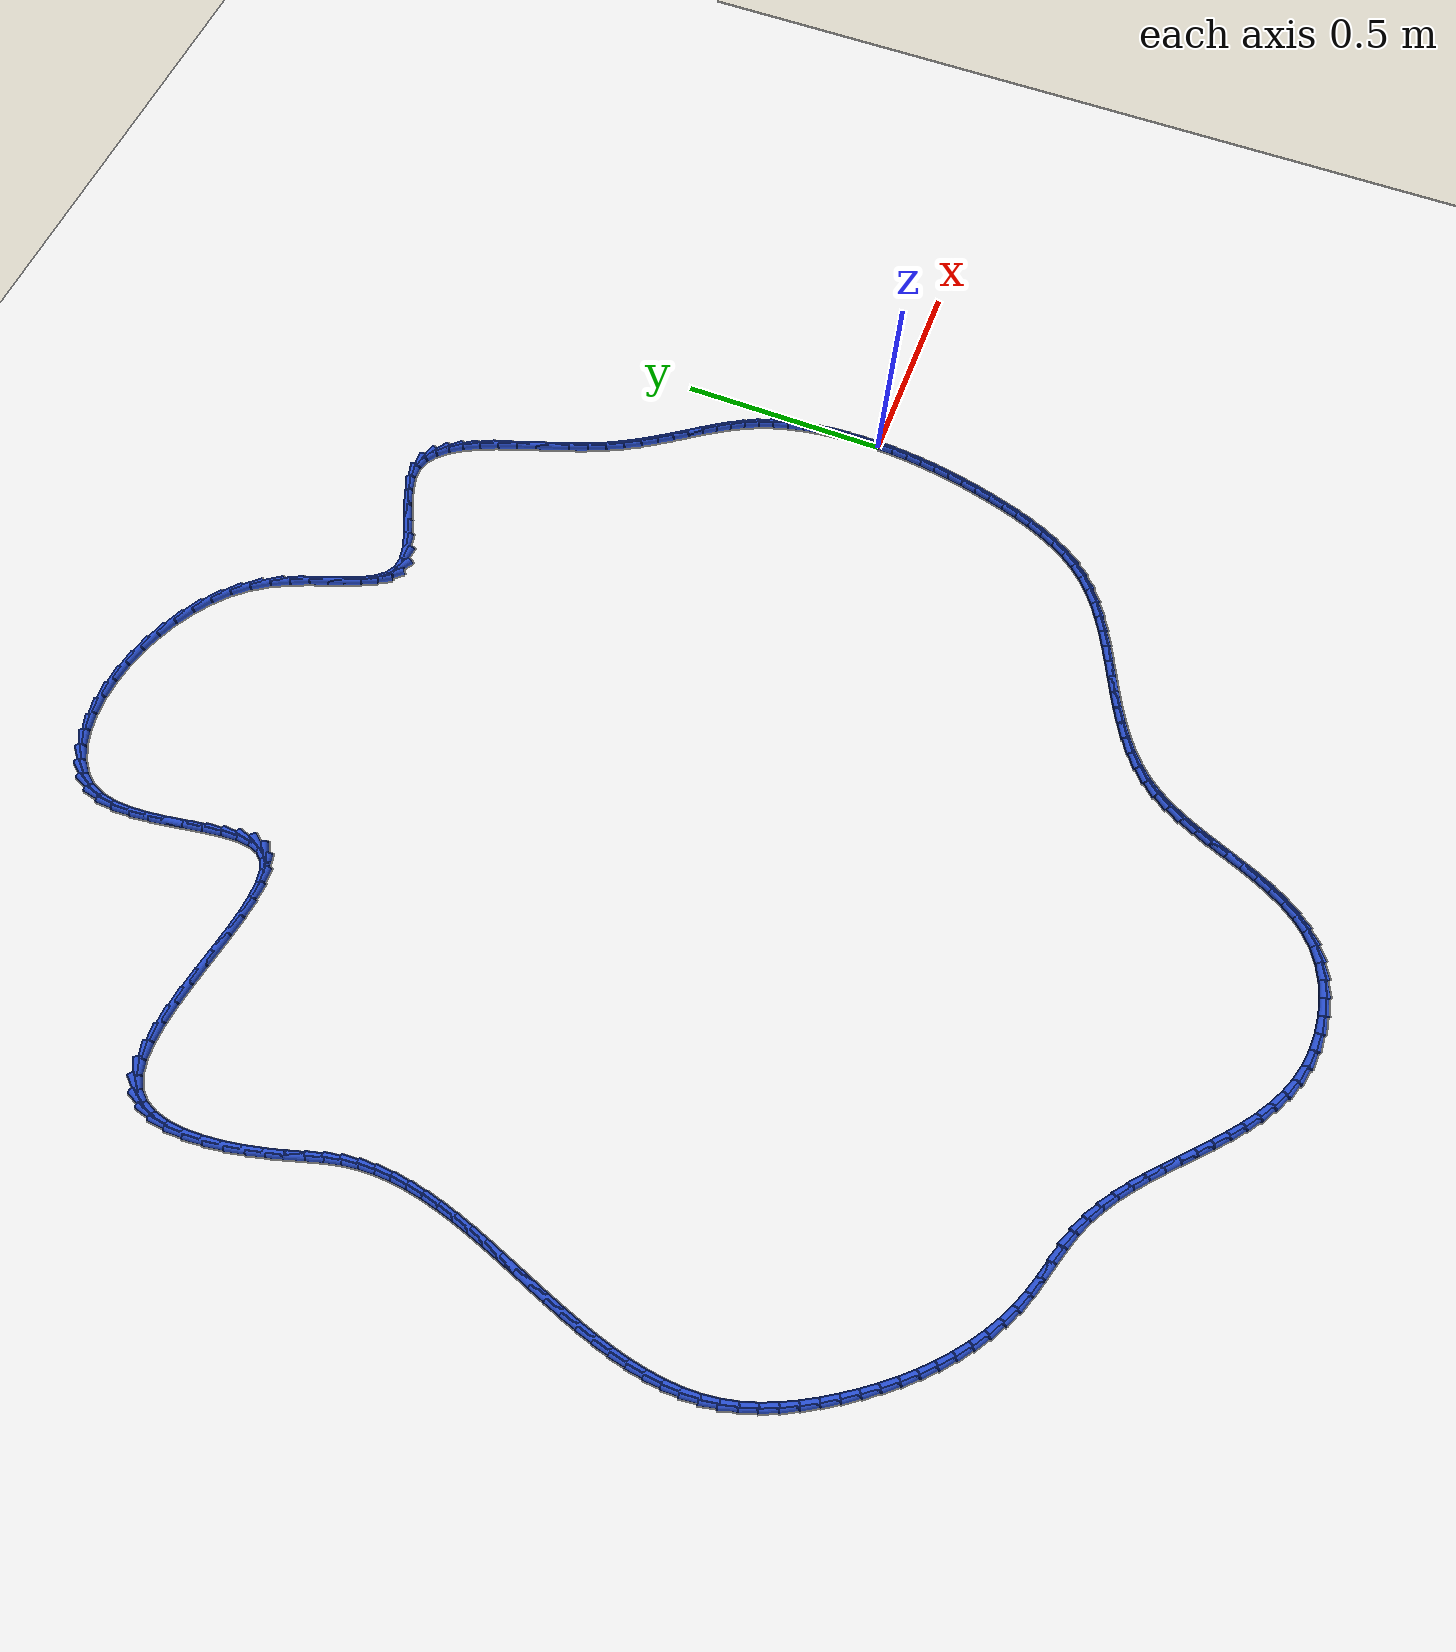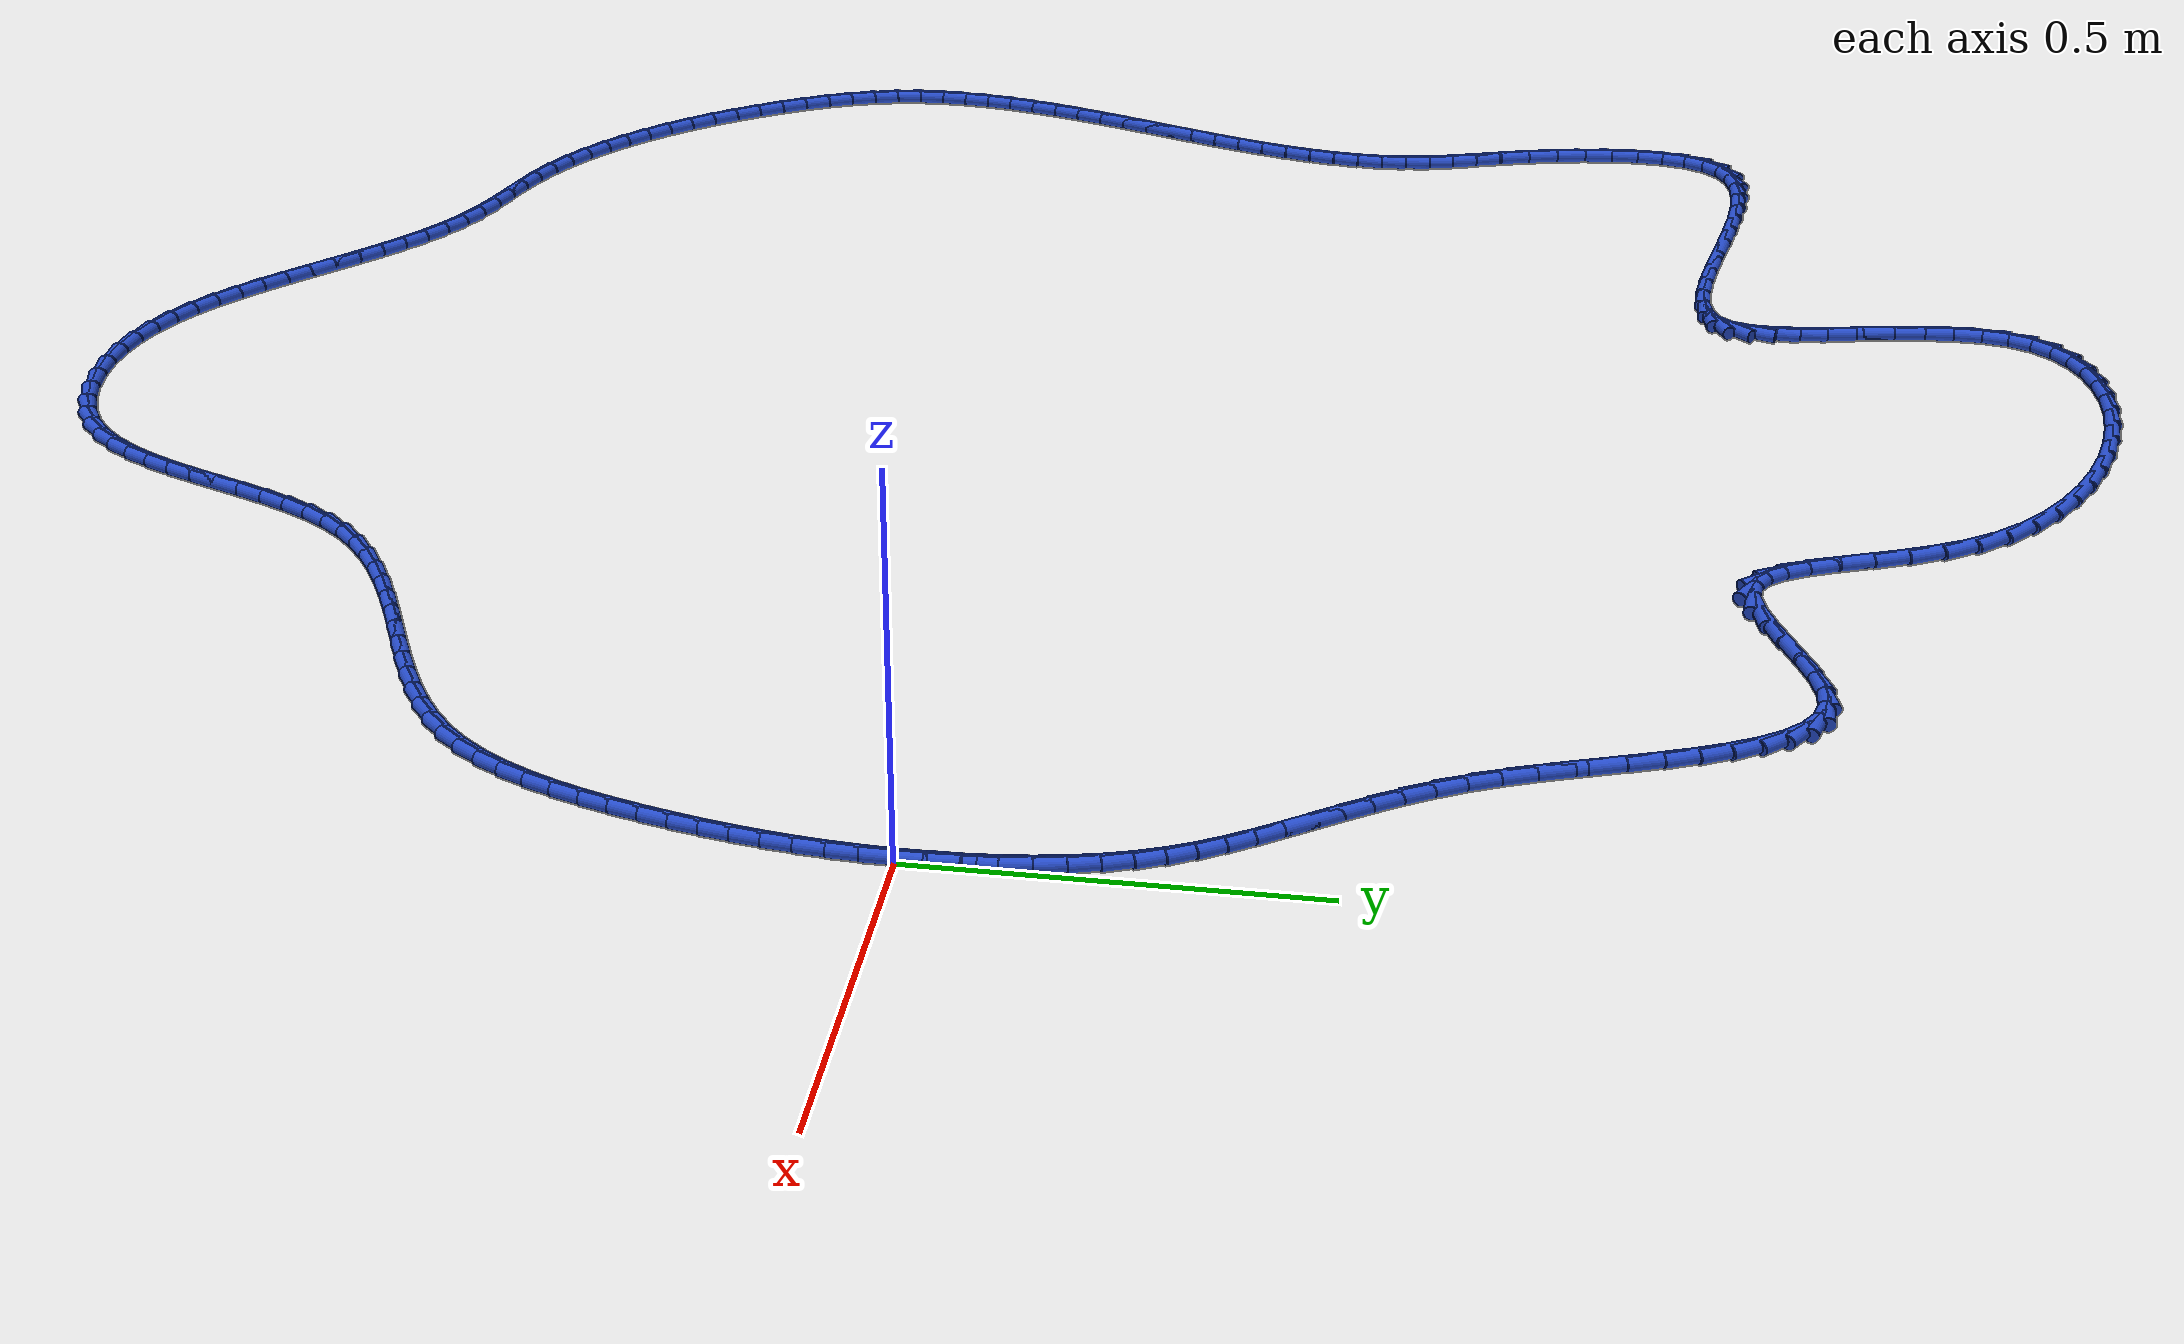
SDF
<sdf version="1.6">
 <world name="default">
  <light name="sun" type="directional">
   <pose>0 0 10 0 -0 0</pose>
   <diffuse>0.8 0.8 0.8 1</diffuse>
   <specular>0.2 0.2 0.2 1</specular>
   <attenuation>
    <range>1000</range>
    <constant>0.9</constant>
    <linear>0.01</linear>
    <quadratic>0.001</quadratic>
   </attenuation>
   <direction>-0.5 0.1 -0.9</direction>
  </light>
  <model name="ground_plane">
   <static>1</static>
   <link name="link">
    <collision name="collision">
     <geometry><plane><normal>0 0 1</normal><size>100 100</size></plane></geometry>
     <surface><friction><ode><mu>100</mu><mu2>50</mu2></ode></friction></surface>
    </collision>
    <visual name="visual">
     <cast_shadows>0</cast_shadows>
     <geometry><plane><normal>0 0 1</normal><size>100 100</size></plane></geometry>
     <material>
      <script><uri>file://media/materials/scripts/gazebo.material</uri><name>Gazebo/WhiteGlow</name></script>
     </material>
    </visual>
   </link>
  </model>
  <gravity>0 0 -9.8</gravity>
  <magnetic_field>6e-06 2.3e-05 -4.2e-05</magnetic_field>
  <atmosphere type="adiabatic"/>
  <physics name="default_physics" default="0" type="ode">
   <max_step_size>0.001</max_step_size>
   <real_time_factor>1</real_time_factor>
   <real_time_update_rate>1000</real_time_update_rate>
  </physics>
  <scene><ambient>0.4 0.4 0.4 1</ambient><background>0.7 0.7 0.7 1</background><shadows>1</shadows></scene>
  <spherical_coordinates>
   <surface_model>EARTH_WGS84</surface_model>
   <latitude_deg>0</latitude_deg>
   <longitude_deg>0</longitude_deg>
   <elevation>0</elevation>
   <heading_deg>0</heading_deg>
  </spherical_coordinates>
  <model name="line">
   <link name="link_0">
    <pose>-1.3010426069826053e-18 -6.938893903907228e-18 0.01 0 1.57 1.5634827013449681</pose>
    <collision name="collision">
     <geometry><cylinder><radius>0.01</radius><length>0.08</length></cylinder></geometry>
    </collision>
    <visual name="visual">
     <material>
      <script><name>Gazebo/Blue</name><uri>file://media/materials/scripts/gazebo.material</uri></script>
     </material>
     <geometry><cylinder><radius>0.01</radius><length>0.08</length></cylinder></geometry>
    </visual>
   </link>
   <link name="link_1">
    <pose>0.0002860031846336292 0.0391048307328377 0.01 0 1.57 -1.540701349567161</pose>
    <collision name="collision">
     <geometry><cylinder><radius>0.01</radius><length>0.08</length></cylinder></geometry>
    </collision>
    <visual name="visual">
     <material>
      <script><name>Gazebo/Blue</name><uri>file://media/materials/scripts/gazebo.material</uri></script>
     </material>
     <geometry><cylinder><radius>0.01</radius><length>0.08</length></cylinder></geometry>
    </visual>
   </link>
   <link name="link_2">
    <pose>-0.0008977572656325792 0.07842710831524721 0.01 0 1.57 -1.4993874857138636</pose>
    <collision name="collision">
     <geometry><cylinder><radius>0.01</radius><length>0.08</length></cylinder></geometry>
    </collision>
    <visual name="visual">
     <material>
      <script><name>Gazebo/Blue</name><uri>file://media/materials/scripts/gazebo.material</uri></script>
     </material>
     <geometry><cylinder><radius>0.01</radius><length>0.08</length></cylinder></geometry>
    </visual>
   </link>
   <link name="link_3">
    <pose>-0.003704237645874554 0.11766186448842522 0.01 0 1.57 -1.4533707268006342</pose>
    <collision name="collision">
     <geometry><cylinder><radius>0.01</radius><length>0.08</length></cylinder></geometry>
    </collision>
    <visual name="visual">
     <material>
      <script><name>Gazebo/Blue</name><uri>file://media/materials/scripts/gazebo.material</uri></script>
     </material>
     <geometry><cylinder><radius>0.01</radius><length>0.08</length></cylinder></geometry>
    </visual>
   </link>
   <link name="link_4">
    <pose>-0.008286394251168231 0.15650413099356827 0.01 0 1.57 -1.4017394035858466</pose>
    <collision name="collision">
     <geometry><cylinder><radius>0.01</radius><length>0.08</length></cylinder></geometry>
    </collision>
    <visual name="visual">
     <material>
      <script><name>Gazebo/Blue</name><uri>file://media/materials/scripts/gazebo.material</uri></script>
     </material>
     <geometry><cylinder><radius>0.01</radius><length>0.08</length></cylinder></geometry>
    </visual>
   </link>
   <link name="link_5">
    <pose>-0.01479718337658955 0.1946489395718733 0.01 0 1.57 -1.343459234744967</pose>
    <collision name="collision">
     <geometry><cylinder><radius>0.01</radius><length>0.08</length></cylinder></geometry>
    </collision>
    <visual name="visual">
     <material>
      <script><name>Gazebo/Blue</name><uri>file://media/materials/scripts/gazebo.material</uri></script>
     </material>
     <geometry><cylinder><radius>0.01</radius><length>0.08</length></cylinder></geometry>
    </visual>
   </link>
   <link name="link_6">
    <pose>-0.023389561317214435 0.23179132196453678 0.01 0 1.57 -1.2773840416386868</pose>
    <collision name="collision">
     <geometry><cylinder><radius>0.01</radius><length>0.08</length></cylinder></geometry>
    </collision>
    <visual name="visual">
     <material>
      <script><name>Gazebo/Blue</name><uri>file://media/materials/scripts/gazebo.material</uri></script>
     </material>
     <geometry><cylinder><radius>0.01</radius><length>0.08</length></cylinder></geometry>
    </visual>
   </link>
   <link name="link_7">
    <pose>-0.03421648436811882 0.2676263099127556 0.01 0 1.57 -1.2023362966498445</pose>
    <collision name="collision">
     <geometry><cylinder><radius>0.01</radius><length>0.08</length></cylinder></geometry>
    </collision>
    <visual name="visual">
     <material>
      <script><name>Gazebo/Blue</name><uri>file://media/materials/scripts/gazebo.material</uri></script>
     </material>
     <geometry><cylinder><radius>0.01</radius><length>0.08</length></cylinder></geometry>
    </visual>
   </link>
   <link name="link_8">
    <pose>-0.04743005409304305 0.301850147587034 0.01 0 1.57 -1.123769966900324</pose>
    <collision name="collision">
     <geometry><cylinder><radius>0.01</radius><length>0.08</length></cylinder></geometry>
    </collision>
    <visual name="visual">
     <material>
      <script><name>Gazebo/Blue</name><uri>file://media/materials/scripts/gazebo.material</uri></script>
     </material>
     <geometry><cylinder><radius>0.01</radius><length>0.08</length></cylinder></geometry>
    </visual>
   </link>
   <link name="link_9">
    <pose>-0.06302543961726352 0.33438168651976685 0.01 0 1.57 -1.0569096853207514</pose>
    <collision name="collision">
     <geometry><cylinder><radius>0.01</radius><length>0.08</length></cylinder></geometry>
    </collision>
    <visual name="visual">
     <material>
      <script><name>Gazebo/Blue</name><uri>file://media/materials/scripts/gazebo.material</uri></script>
     </material>
     <geometry><cylinder><radius>0.01</radius><length>0.08</length></cylinder></geometry>
    </visual>
   </link>
   <link name="link_10">
    <pose>-0.08065890200132704 0.36562051652124256 0.01 0 1.57 -1.0056401886785002</pose>
    <collision name="collision">
     <geometry><cylinder><radius>0.01</radius><length>0.08</length></cylinder></geometry>
    </collision>
    <visual name="visual">
     <material>
      <script><name>Gazebo/Blue</name><uri>file://media/materials/scripts/gazebo.material</uri></script>
     </material>
     <geometry><cylinder><radius>0.01</radius><length>0.08</length></cylinder></geometry>
    </visual>
   </link>
   <link name="link_11">
    <pose>-0.09994253710456295 0.3960288753732363 0.01 0 1.57 -0.9709244982020133</pose>
    <collision name="collision">
     <geometry><cylinder><radius>0.01</radius><length>0.08</length></cylinder></geometry>
    </collision>
    <visual name="visual">
     <material>
      <script><name>Gazebo/Blue</name><uri>file://media/materials/scripts/gazebo.material</uri></script>
     </material>
     <geometry><cylinder><radius>0.01</radius><length>0.08</length></cylinder></geometry>
    </visual>
   </link>
   <link name="link_12">
    <pose>-0.12048844078630061 0.4260690008575235 0.01 0 1.57 -0.9528382846766015</pose>
    <collision name="collision">
     <geometry><cylinder><radius>0.01</radius><length>0.08</length></cylinder></geometry>
    </collision>
    <visual name="visual">
     <material>
      <script><name>Gazebo/Blue</name><uri>file://media/materials/scripts/gazebo.material</uri></script>
     </material>
     <geometry><cylinder><radius>0.01</radius><length>0.08</length></cylinder></geometry>
    </visual>
   </link>
   <link name="link_13">
    <pose>-0.1419087089058696 0.45620313075588026 0.01 0 1.57 -0.9508698138442858</pose>
    <collision name="collision">
     <geometry><cylinder><radius>0.01</radius><length>0.08</length></cylinder></geometry>
    </collision>
    <visual name="visual">
     <material>
      <script><name>Gazebo/Blue</name><uri>file://media/materials/scripts/gazebo.material</uri></script>
     </material>
     <geometry><cylinder><radius>0.01</radius><length>0.08</length></cylinder></geometry>
    </visual>
   </link>
   <link name="link_14">
    <pose>-0.16381543732259932 0.48689350285008187 0.01 0 1.57 -0.9641225910992269</pose>
    <collision name="collision">
     <geometry><cylinder><radius>0.01</radius><length>0.08</length></cylinder></geometry>
    </collision>
    <visual name="visual">
     <material>
      <script><name>Gazebo/Blue</name><uri>file://media/materials/scripts/gazebo.material</uri></script>
     </material>
     <geometry><cylinder><radius>0.01</radius><length>0.08</length></cylinder></geometry>
    </visual>
   </link>
   <link name="link_15">
    <pose>-0.1858207218958191 0.5186023549219038 0.01 0 1.57 -0.9914041739318887</pose>
    <collision name="collision">
     <geometry><cylinder><radius>0.01</radius><length>0.08</length></cylinder></geometry>
    </collision>
    <visual name="visual">
     <material>
      <script><name>Gazebo/Blue</name><uri>file://media/materials/scripts/gazebo.material</uri></script>
     </material>
     <geometry><cylinder><radius>0.01</radius><length>0.08</length></cylinder></geometry>
    </visual>
   </link>
   <link name="link_16">
    <pose>-0.2075366584848584 0.5517919247531216 0.01 0 1.57 -1.0312318180430817</pose>
    <collision name="collision">
     <geometry><cylinder><radius>0.01</radius><length>0.08</length></cylinder></geometry>
    </collision>
    <visual name="visual">
     <material>
      <script><name>Gazebo/Blue</name><uri>file://media/materials/scripts/gazebo.material</uri></script>
     </material>
     <geometry><cylinder><radius>0.01</radius><length>0.08</length></cylinder></geometry>
    </visual>
   </link>
   <link name="link_17">
    <pose>-0.22857534294904663 0.5869244501255109 0.01 0 1.57 -1.0818057605773006</pose>
    <collision name="collision">
     <geometry><cylinder><radius>0.01</radius><length>0.08</length></cylinder></geometry>
    </collision>
    <visual name="visual">
     <material>
      <script><name>Gazebo/Blue</name><uri>file://media/materials/scripts/gazebo.material</uri></script>
     </material>
     <geometry><cylinder><radius>0.01</radius><length>0.08</length></cylinder></geometry>
    </visual>
   </link>
   <link name="link_18">
    <pose>-0.2485488711477133 0.6244621688208473 0.01 0 1.57 -1.1405402441898806</pose>
    <collision name="collision">
     <geometry><cylinder><radius>0.01</radius><length>0.08</length></cylinder></geometry>
    </collision>
    <visual name="visual">
     <material>
      <script><name>Gazebo/Blue</name><uri>file://media/materials/scripts/gazebo.material</uri></script>
     </material>
     <geometry><cylinder><radius>0.01</radius><length>0.08</length></cylinder></geometry>
    </visual>
   </link>
   <link name="link_19">
    <pose>-0.2670817480333362 0.664844877062652 0.01 0 1.57 -1.1920426459754478</pose>
    <collision name="collision">
     <geometry><cylinder><radius>0.01</radius><length>0.08</length></cylinder></geometry>
    </collision>
    <visual name="visual">
     <material>
      <script><name>Gazebo/Blue</name><uri>file://media/materials/scripts/gazebo.material</uri></script>
     </material>
     <geometry><cylinder><radius>0.01</radius><length>0.08</length></cylinder></geometry>
    </visual>
   </link>
   <link name="link_20">
    <pose>-0.2841831626674108 0.7078166787511693 0.01 0 1.57 -1.2230222389523542</pose>
    <collision name="collision">
     <geometry><cylinder><radius>0.01</radius><length>0.08</length></cylinder></geometry>
    </collision>
    <visual name="visual">
     <material>
      <script><name>Gazebo/Blue</name><uri>file://media/materials/scripts/gazebo.material</uri></script>
     </material>
     <geometry><cylinder><radius>0.01</radius><length>0.08</length></cylinder></geometry>
    </visual>
   </link>
   <link name="link_21">
    <pose>-0.30031186336751287 0.7523086602588065 0.01 0 1.57 -1.2355864044533307</pose>
    <collision name="collision">
     <geometry><cylinder><radius>0.01</radius><length>0.08</length></cylinder></geometry>
    </collision>
    <visual name="visual">
     <material>
      <script><name>Gazebo/Blue</name><uri>file://media/materials/scripts/gazebo.material</uri></script>
     </material>
     <geometry><cylinder><radius>0.01</radius><length>0.08</length></cylinder></geometry>
    </visual>
   </link>
   <link name="link_22">
    <pose>-0.31595208144126036 0.7972058225592461 0.01 0 1.57 -1.230690257011214</pose>
    <collision name="collision">
     <geometry><cylinder><radius>0.01</radius><length>0.08</length></cylinder></geometry>
    </collision>
    <visual name="visual">
     <material>
      <script><name>Gazebo/Blue</name><uri>file://media/materials/scripts/gazebo.material</uri></script>
     </material>
     <geometry><cylinder><radius>0.01</radius><length>0.08</length></cylinder></geometry>
    </visual>
   </link>
   <link name="link_23">
    <pose>-0.33158804819627113 0.8413931666261711 0.01 0 1.57 -1.2072742325701524</pose>
    <collision name="collision">
     <geometry><cylinder><radius>0.01</radius><length>0.08</length></cylinder></geometry>
    </collision>
    <visual name="visual">
     <material>
      <script><name>Gazebo/Blue</name><uri>file://media/materials/scripts/gazebo.material</uri></script>
     </material>
     <geometry><cylinder><radius>0.01</radius><length>0.08</length></cylinder></geometry>
    </visual>
   </link>
   <link name="link_24">
    <pose>-0.34770399494016346 0.8837556934332651 0.01 0 1.57 -1.161952920179598</pose>
    <collision name="collision">
     <geometry><cylinder><radius>0.01</radius><length>0.08</length></cylinder></geometry>
    </collision>
    <visual name="visual">
     <material>
      <script><name>Gazebo/Blue</name><uri>file://media/materials/scripts/gazebo.material</uri></script>
     </material>
     <geometry><cylinder><radius>0.01</radius><length>0.08</length></cylinder></geometry>
    </visual>
   </link>
   <link name="link_25">
    <pose>-0.3647841529805552 0.9231784039542107 0.01 0 1.57 -1.0882262288710491</pose>
    <collision name="collision">
     <geometry><cylinder><radius>0.01</radius><length>0.08</length></cylinder></geometry>
    </collision>
    <visual name="visual">
     <material>
      <script><name>Gazebo/Blue</name><uri>file://media/materials/scripts/gazebo.material</uri></script>
     </material>
     <geometry><cylinder><radius>0.01</radius><length>0.08</length></cylinder></geometry>
    </visual>
   </link>
   <link name="link_26">
    <pose>-0.3833127536250644 0.958546299162691 0.01 0 1.57 -0.9752840862644171</pose>
    <collision name="collision">
     <geometry><cylinder><radius>0.01</radius><length>0.08</length></cylinder></geometry>
    </collision>
    <visual name="visual">
     <material>
      <script><name>Gazebo/Blue</name><uri>file://media/materials/scripts/gazebo.material</uri></script>
     </material>
     <geometry><cylinder><radius>0.01</radius><length>0.08</length></cylinder></geometry>
    </visual>
   </link>
   <link name="link_27">
    <pose>-0.4037740281813093 0.9887443800323892 0.01 0 1.57 -0.8075158579327568</pose>
    <collision name="collision">
     <geometry><cylinder><radius>0.01</radius><length>0.08</length></cylinder></geometry>
    </collision>
    <visual name="visual">
     <material>
      <script><name>Gazebo/Blue</name><uri>file://media/materials/scripts/gazebo.material</uri></script>
     </material>
     <geometry><cylinder><radius>0.01</radius><length>0.08</length></cylinder></geometry>
    </visual>
   </link>
   <link name="link_28">
    <pose>-0.42665220795690784 1.0126576475369884 0.01 0 1.57 -0.5697174143870546</pose>
    <collision name="collision">
     <geometry><cylinder><radius>0.01</radius><length>0.08</length></cylinder></geometry>
    </collision>
    <visual name="visual">
     <material>
      <script><name>Gazebo/Blue</name><uri>file://media/materials/scripts/gazebo.material</uri></script>
     </material>
     <geometry><cylinder><radius>0.01</radius><length>0.08</length></cylinder></geometry>
    </visual>
   </link>
   <link name="link_29">
    <pose>-0.45243152425947775 1.0291711026501713 0.01 0 1.57 -0.26767611321087653</pose>
    <collision name="collision">
     <geometry><cylinder><radius>0.01</radius><length>0.08</length></cylinder></geometry>
    </collision>
    <visual name="visual">
     <material>
      <script><name>Gazebo/Blue</name><uri>file://media/materials/scripts/gazebo.material</uri></script>
     </material>
     <geometry><cylinder><radius>0.01</radius><length>0.08</length></cylinder></geometry>
    </visual>
   </link>
   <link name="link_30">
    <pose>-0.4815962083966374 1.037169746345621 0.01 0 1.57 0.047332688127085285</pose>
    <collision name="collision">
     <geometry><cylinder><radius>0.01</radius><length>0.08</length></cylinder></geometry>
    </collision>
    <visual name="visual">
     <material>
      <script><name>Gazebo/Blue</name><uri>file://media/materials/scripts/gazebo.material</uri></script>
     </material>
     <geometry><cylinder><radius>0.01</radius><length>0.08</length></cylinder></geometry>
    </visual>
   </link>
   <link name="link_31">
    <pose>-0.5146005050724667 1.0356063965888667 0.01 0 1.57 0.274340062868435</pose>
    <collision name="collision">
     <geometry><cylinder><radius>0.01</radius><length>0.08</length></cylinder></geometry>
    </collision>
    <visual name="visual">
     <material>
      <script><name>Gazebo/Blue</name><uri>file://media/materials/scripts/gazebo.material</uri></script>
     </material>
     <geometry><cylinder><radius>0.01</radius><length>0.08</length></cylinder></geometry>
    </visual>
   </link>
   <link name="link_32">
    <pose>-0.5510525209742163 1.0253474770298956 0.01 0 1.57 0.39226820996565503</pose>
    <collision name="collision">
     <geometry><cylinder><radius>0.01</radius><length>0.08</length></cylinder></geometry>
    </collision>
    <visual name="visual">
     <material>
      <script><name>Gazebo/Blue</name><uri>file://media/materials/scripts/gazebo.material</uri></script>
     </material>
     <geometry><cylinder><radius>0.01</radius><length>0.08</length></cylinder></geometry>
    </visual>
   </link>
   <link name="link_33">
    <pose>-0.5896169392094083 1.0093930357264294 0.01 0 1.57 0.44083358409011675</pose>
    <collision name="collision">
     <geometry><cylinder><radius>0.01</radius><length>0.08</length></cylinder></geometry>
    </collision>
    <visual name="visual">
     <material>
      <script><name>Gazebo/Blue</name><uri>file://media/materials/scripts/gazebo.material</uri></script>
     </material>
     <geometry><cylinder><radius>0.01</radius><length>0.08</length></cylinder></geometry>
    </visual>
   </link>
   <link name="link_34">
    <pose>-0.6289089268959585 0.9908551049247001 0.01 0 1.57 0.4361987942885245</pose>
    <collision name="collision">
     <geometry><cylinder><radius>0.01</radius><length>0.08</length></cylinder></geometry>
    </collision>
    <visual name="visual">
     <material>
      <script><name>Gazebo/Blue</name><uri>file://media/materials/scripts/gazebo.material</uri></script>
     </material>
     <geometry><cylinder><radius>0.01</radius><length>0.08</length></cylinder></geometry>
    </visual>
   </link>
   <link name="link_35">
    <pose>-0.6675436511517829 0.9728457168709397 0.01 0 1.57 0.3741711489900024</pose>
    <collision name="collision">
     <geometry><cylinder><radius>0.01</radius><length>0.08</length></cylinder></geometry>
    </collision>
    <visual name="visual">
     <material>
      <script><name>Gazebo/Blue</name><uri>file://media/materials/scripts/gazebo.material</uri></script>
     </material>
     <geometry><cylinder><radius>0.01</radius><length>0.08</length></cylinder></geometry>
    </visual>
   </link>
   <link name="link_36">
    <pose>-0.7041362790947978 0.9584769038113803 0.01 0 1.57 0.22572744383465707</pose>
    <collision name="collision">
     <geometry><cylinder><radius>0.01</radius><length>0.08</length></cylinder></geometry>
    </collision>
    <visual name="visual">
     <material>
      <script><name>Gazebo/Blue</name><uri>file://media/materials/scripts/gazebo.material</uri></script>
     </material>
     <geometry><cylinder><radius>0.01</radius><length>0.08</length></cylinder></geometry>
    </visual>
   </link>
   <link name="link_37">
    <pose>-0.737301977842919 0.9508606979922531 0.01 0 1.57 -0.07740267034636182</pose>
    <collision name="collision">
     <geometry><cylinder><radius>0.01</radius><length>0.08</length></cylinder></geometry>
    </collision>
    <visual name="visual">
     <material>
      <script><name>Gazebo/Blue</name><uri>file://media/materials/scripts/gazebo.material</uri></script>
     </material>
     <geometry><cylinder><radius>0.01</radius><length>0.08</length></cylinder></geometry>
    </visual>
   </link>
   <link name="link_38">
    <pose>-0.7656817503220757 0.9530617655818225 0.01 0 1.57 -0.5123504061385515</pose>
    <collision name="collision">
     <geometry><cylinder><radius>0.01</radius><length>0.08</length></cylinder></geometry>
    </collision>
    <visual name="visual">
     <material>
      <script><name>Gazebo/Blue</name><uri>file://media/materials/scripts/gazebo.material</uri></script>
     </material>
     <geometry><cylinder><radius>0.01</radius><length>0.08</length></cylinder></geometry>
    </visual>
   </link>
   <link name="link_39">
    <pose>-0.7889922523363688 0.9661727245713243 0.01 0 1.57 -0.8587184407550742</pose>
    <collision name="collision">
     <geometry><cylinder><radius>0.01</radius><length>0.08</length></cylinder></geometry>
    </collision>
    <visual name="visual">
     <material>
      <script><name>Gazebo/Blue</name><uri>file://media/materials/scripts/gazebo.material</uri></script>
     </material>
     <geometry><cylinder><radius>0.01</radius><length>0.08</length></cylinder></geometry>
    </visual>
   </link>
   <link name="link_40">
    <pose>-0.8083901491474638 0.9886461516493418 0.01 0 1.57 -1.0632357945586735</pose>
    <collision name="collision">
     <geometry><cylinder><radius>0.01</radius><length>0.08</length></cylinder></geometry>
    </collision>
    <visual name="visual">
     <material>
      <script><name>Gazebo/Blue</name><uri>file://media/materials/scripts/gazebo.material</uri></script>
     </material>
     <geometry><cylinder><radius>0.01</radius><length>0.08</length></cylinder></geometry>
    </visual>
   </link>
   <link name="link_41">
    <pose>-0.825132762707907 1.0187500845627737 0.01 0 1.57 -1.167900381079779</pose>
    <collision name="collision">
     <geometry><cylinder><radius>0.01</radius><length>0.08</length></cylinder></geometry>
    </collision>
    <visual name="visual">
     <material>
      <script><name>Gazebo/Blue</name><uri>file://media/materials/scripts/gazebo.material</uri></script>
     </material>
     <geometry><cylinder><radius>0.01</radius><length>0.08</length></cylinder></geometry>
    </visual>
   </link>
   <link name="link_42">
    <pose>-0.8404774149702444 1.054752561058519 0.01 0 1.57 -1.2089601656349578</pose>
    <collision name="collision">
     <geometry><cylinder><radius>0.01</radius><length>0.08</length></cylinder></geometry>
    </collision>
    <visual name="visual">
     <material>
      <script><name>Gazebo/Blue</name><uri>file://media/materials/scripts/gazebo.material</uri></script>
     </material>
     <geometry><cylinder><radius>0.01</radius><length>0.08</length></cylinder></geometry>
    </visual>
   </link>
   <link name="link_43">
    <pose>-0.855681427887023 1.0949216188834767 0.01 0 1.57 -1.2049590898502867</pose>
    <collision name="collision">
     <geometry><cylinder><radius>0.01</radius><length>0.08</length></cylinder></geometry>
    </collision>
    <visual name="visual">
     <material>
      <script><name>Gazebo/Blue</name><uri>file://media/materials/scripts/gazebo.material</uri></script>
     </material>
     <geometry><cylinder><radius>0.01</radius><length>0.08</length></cylinder></geometry>
    </visual>
   </link>
   <link name="link_44">
    <pose>-0.8720021234107886 1.1375252957845465 0.01 0 1.57 -1.163276972246386</pose>
    <collision name="collision">
     <geometry><cylinder><radius>0.01</radius><length>0.08</length></cylinder></geometry>
    </collision>
    <visual name="visual">
     <material>
      <script><name>Gazebo/Blue</name><uri>file://media/materials/scripts/gazebo.material</uri></script>
     </material>
     <geometry><cylinder><radius>0.01</radius><length>0.08</length></cylinder></geometry>
    </visual>
   </link>
   <link name="link_45">
    <pose>-0.890696823494088 1.1808316295086265 0.01 0 1.57 -1.0849309760015116</pose>
    <collision name="collision">
     <geometry><cylinder><radius>0.01</radius><length>0.08</length></cylinder></geometry>
    </collision>
    <visual name="visual">
     <material>
      <script><name>Gazebo/Blue</name><uri>file://media/materials/scripts/gazebo.material</uri></script>
     </material>
     <geometry><cylinder><radius>0.01</radius><length>0.08</length></cylinder></geometry>
    </visual>
   </link>
   <link name="link_46">
    <pose>-0.9130228500894665 1.2231086578026156 0.01 0 1.57 -0.9680348446010532</pose>
    <collision name="collision">
     <geometry><cylinder><radius>0.01</radius><length>0.08</length></cylinder></geometry>
    </collision>
    <visual name="visual">
     <material>
      <script><name>Gazebo/Blue</name><uri>file://media/materials/scripts/gazebo.material</uri></script>
     </material>
     <geometry><cylinder><radius>0.01</radius><length>0.08</length></cylinder></geometry>
    </visual>
   </link>
   <link name="link_47">
    <pose>-0.9402245717623101 1.262634641905796 0.01 0 1.57 -0.831123517315011</pose>
    <collision name="collision">
     <geometry><cylinder><radius>0.01</radius><length>0.08</length></cylinder></geometry>
    </collision>
    <visual name="visual">
     <material>
      <script><name>Gazebo/Blue</name><uri>file://media/materials/scripts/gazebo.material</uri></script>
     </material>
     <geometry><cylinder><radius>0.01</radius><length>0.08</length></cylinder></geometry>
    </visual>
   </link>
   <link name="link_48">
    <pose>-0.9727696386613364 1.298300869960585 0.01 0 1.57 -0.7055583168124736</pose>
    <collision name="collision">
     <geometry><cylinder><radius>0.01</radius><length>0.08</length></cylinder></geometry>
    </collision>
    <visual name="visual">
     <material>
      <script><name>Gazebo/Blue</name><uri>file://media/materials/scripts/gazebo.material</uri></script>
     </material>
     <geometry><cylinder><radius>0.01</radius><length>0.08</length></cylinder></geometry>
    </visual>
   </link>
   <link name="link_49">
    <pose>-1.0099220660741948 1.3299486018566278 0.01 0 1.57 -0.592590140321586</pose>
    <collision name="collision">
     <geometry><cylinder><radius>0.01</radius><length>0.08</length></cylinder></geometry>
    </collision>
    <visual name="visual">
     <material>
      <script><name>Gazebo/Blue</name><uri>file://media/materials/scripts/gazebo.material</uri></script>
     </material>
     <geometry><cylinder><radius>0.01</radius><length>0.08</length></cylinder></geometry>
    </visual>
   </link>
   <link name="link_50">
    <pose>-1.0508423633708652 1.3575007897813218 0.01 0 1.57 -0.48984431248607013</pose>
    <collision name="collision">
     <geometry><cylinder><radius>0.01</radius><length>0.08</length></cylinder></geometry>
    </collision>
    <visual name="visual">
     <material>
      <script><name>Gazebo/Blue</name><uri>file://media/materials/scripts/gazebo.material</uri></script>
     </material>
     <geometry><cylinder><radius>0.01</radius><length>0.08</length></cylinder></geometry>
    </visual>
   </link>
   <link name="link_51">
    <pose>-1.0946910399213288 1.3808803859220669 0.01 0 1.57 -0.3945927161951832</pose>
    <collision name="collision">
     <geometry><cylinder><radius>0.01</radius><length>0.08</length></cylinder></geometry>
    </collision>
    <visual name="visual">
     <material>
      <script><name>Gazebo/Blue</name><uri>file://media/materials/scripts/gazebo.material</uri></script>
     </material>
     <geometry><cylinder><radius>0.01</radius><length>0.08</length></cylinder></geometry>
    </visual>
   </link>
   <link name="link_52">
    <pose>-1.1406286050955652 1.4000103424662607 0.01 0 1.57 -0.3039916010189863</pose>
    <collision name="collision">
     <geometry><cylinder><radius>0.01</radius><length>0.08</length></cylinder></geometry>
    </collision>
    <visual name="visual">
     <material>
      <script><name>Gazebo/Blue</name><uri>file://media/materials/scripts/gazebo.material</uri></script>
     </material>
     <geometry><cylinder><radius>0.01</radius><length>0.08</length></cylinder></geometry>
    </visual>
   </link>
   <link name="link_53">
    <pose>-1.1878155682635552 1.4148136116013017 0.01 0 1.57 -0.21511143782192918</pose>
    <collision name="collision">
     <geometry><cylinder><radius>0.01</radius><length>0.08</length></cylinder></geometry>
    </collision>
    <visual name="visual">
     <material>
      <script><name>Gazebo/Blue</name><uri>file://media/materials/scripts/gazebo.material</uri></script>
     </material>
     <geometry><cylinder><radius>0.01</radius><length>0.08</length></cylinder></geometry>
    </visual>
   </link>
   <link name="link_54">
    <pose>-1.2354124387952785 1.4252131455145887 0.01 0 1.57 -0.12483174964531954</pose>
    <collision name="collision">
     <geometry><cylinder><radius>0.01</radius><length>0.08</length></cylinder></geometry>
    </collision>
    <visual name="visual">
     <material>
      <script><name>Gazebo/Blue</name><uri>file://media/materials/scripts/gazebo.material</uri></script>
     </material>
     <geometry><cylinder><radius>0.01</radius><length>0.08</length></cylinder></geometry>
    </visual>
   </link>
   <link name="link_55">
    <pose>-1.2825797260607152 1.43113189639352 0.01 0 1.57 -0.029642143232625876</pose>
    <collision name="collision">
     <geometry><cylinder><radius>0.01</radius><length>0.08</length></cylinder></geometry>
    </collision>
    <visual name="visual">
     <material>
      <script><name>Gazebo/Blue</name><uri>file://media/materials/scripts/gazebo.material</uri></script>
     </material>
     <geometry><cylinder><radius>0.01</radius><length>0.08</length></cylinder></geometry>
    </visual>
   </link>
   <link name="link_56">
    <pose>-1.3284779394298478 1.4324928164254944 0.01 0 1.57 0.07462673791602278</pose>
    <collision name="collision">
     <geometry><cylinder><radius>0.01</radius><length>0.08</length></cylinder></geometry>
    </collision>
    <visual name="visual">
     <material>
      <script><name>Gazebo/Blue</name><uri>file://media/materials/scripts/gazebo.material</uri></script>
     </material>
     <geometry><cylinder><radius>0.01</radius><length>0.08</length></cylinder></geometry>
    </visual>
   </link>
   <link name="link_57">
    <pose>-1.3722675882726536 1.4292188577979104 0.01 0 1.57 0.19309683698919666</pose>
    <collision name="collision">
     <geometry><cylinder><radius>0.01</radius><length>0.08</length></cylinder></geometry>
    </collision>
    <visual name="visual">
     <material>
      <script><name>Gazebo/Blue</name><uri>file://media/materials/scripts/gazebo.material</uri></script>
     </material>
     <geometry><cylinder><radius>0.01</radius><length>0.08</length></cylinder></geometry>
    </visual>
   </link>
   <link name="link_58">
    <pose>-1.4131091819591144 1.421232972698166 0.01 0 1.57 0.33200161515533416</pose>
    <collision name="collision">
     <geometry><cylinder><radius>0.01</radius><length>0.08</length></cylinder></geometry>
    </collision>
    <visual name="visual">
     <material>
      <script><name>Gazebo/Blue</name><uri>file://media/materials/scripts/gazebo.material</uri></script>
     </material>
     <geometry><cylinder><radius>0.01</radius><length>0.08</length></cylinder></geometry>
    </visual>
   </link>
   <link name="link_59">
    <pose>-1.4501632298592102 1.40845811331366 0.01 0 1.57 0.498238991069275</pose>
    <collision name="collision">
     <geometry><cylinder><radius>0.01</radius><length>0.08</length></cylinder></geometry>
    </collision>
    <visual name="visual">
     <material>
      <script><name>Gazebo/Blue</name><uri>file://media/materials/scripts/gazebo.material</uri></script>
     </material>
     <geometry><cylinder><radius>0.01</radius><length>0.08</length></cylinder></geometry>
    </visual>
   </link>
   <link name="link_60">
    <pose>-1.4825902413429226 1.3908172318317915 0.01 0 1.57 0.6972913482822033</pose>
    <collision name="collision">
     <geometry><cylinder><radius>0.01</radius><length>0.08</length></cylinder></geometry>
    </collision>
    <visual name="visual">
     <material>
      <script><name>Gazebo/Blue</name><uri>file://media/materials/scripts/gazebo.material</uri></script>
     </material>
     <geometry><cylinder><radius>0.01</radius><length>0.08</length></cylinder></geometry>
    </visual>
   </link>
   <link name="link_61">
    <pose>-1.5095507257802299 1.3682332804399575 0.01 0 1.57 0.9284226143455631</pose>
    <collision name="collision">
     <geometry><cylinder><radius>0.01</radius><length>0.08</length></cylinder></geometry>
    </collision>
    <visual name="visual">
     <material>
      <script><name>Gazebo/Blue</name><uri>file://media/materials/scripts/gazebo.material</uri></script>
     </material>
     <geometry><cylinder><radius>0.01</radius><length>0.08</length></cylinder></geometry>
    </visual>
   </link>
   <link name="link_62">
    <pose>-1.5302051925411133 1.3406292113255578 0.01 0 1.57 1.178719840497818</pose>
    <collision name="collision">
     <geometry><cylinder><radius>0.01</radius><length>0.08</length></cylinder></geometry>
    </collision>
    <visual name="visual">
     <material>
      <script><name>Gazebo/Blue</name><uri>file://media/materials/scripts/gazebo.material</uri></script>
     </material>
     <geometry><cylinder><radius>0.01</radius><length>0.08</length></cylinder></geometry>
    </visual>
   </link>
   <link name="link_63">
    <pose>-1.5437243359167478 1.307933550936087 0.01 0 1.57 1.4023511764040069</pose>
    <collision name="collision">
     <geometry><cylinder><radius>0.01</radius><length>0.08</length></cylinder></geometry>
    </collision>
    <visual name="visual">
     <material>
      <script><name>Gazebo/Blue</name><uri>file://media/materials/scripts/gazebo.material</uri></script>
     </material>
     <geometry><cylinder><radius>0.01</radius><length>0.08</length></cylinder></geometry>
    </visual>
   </link>
   <link name="link_64">
    <pose>-1.5500872237389078 1.2705172527427155 0.01 0 1.57 1.5569566997113287</pose>
    <collision name="collision">
     <geometry><cylinder><radius>0.01</radius><length>0.08</length></cylinder></geometry>
    </collision>
    <visual name="visual">
     <material>
      <script><name>Gazebo/Blue</name><uri>file://media/materials/scripts/gazebo.material</uri></script>
     </material>
     <geometry><cylinder><radius>0.01</radius><length>0.08</length></cylinder></geometry>
    </visual>
   </link>
   <link name="link_65">
    <pose>-1.5506548184404134 1.229507588285756 0.01 0 1.57 -1.4850334992907446</pose>
    <collision name="collision">
     <geometry><cylinder><radius>0.01</radius><length>0.08</length></cylinder></geometry>
    </collision>
    <visual name="visual">
     <material>
      <script><name>Gazebo/Blue</name><uri>file://media/materials/scripts/gazebo.material</uri></script>
     </material>
     <geometry><cylinder><radius>0.01</radius><length>0.08</length></cylinder></geometry>
    </visual>
   </link>
   <link name="link_66">
    <pose>-1.5469234136646428 1.1861058965776632 0.01 0 1.57 -1.425301975199581</pose>
    <collision name="collision">
     <geometry><cylinder><radius>0.01</radius><length>0.08</length></cylinder></geometry>
    </collision>
    <visual name="visual">
     <material>
      <script><name>Gazebo/Blue</name><uri>file://media/materials/scripts/gazebo.material</uri></script>
     </material>
     <geometry><cylinder><radius>0.01</radius><length>0.08</length></cylinder></geometry>
    </visual>
   </link>
   <link name="link_67">
    <pose>-1.5403893030549747 1.1415135166308916 0.01 0 1.57 -1.3967080713000692</pose>
    <collision name="collision">
     <geometry><cylinder><radius>0.01</radius><length>0.08</length></cylinder></geometry>
    </collision>
    <visual name="visual">
     <material>
      <script><name>Gazebo/Blue</name><uri>file://media/materials/scripts/gazebo.material</uri></script>
     </material>
     <geometry><cylinder><radius>0.01</radius><length>0.08</length></cylinder></geometry>
    </visual>
   </link>
   <link name="link_68">
    <pose>-1.532548780254787 1.0969317874578945 0.01 0 1.57 -1.3961876806317168</pose>
    <collision name="collision">
     <geometry><cylinder><radius>0.01</radius><length>0.08</length></cylinder></geometry>
    </collision>
    <visual name="visual">
     <material>
      <script><name>Gazebo/Blue</name><uri>file://media/materials/scripts/gazebo.material</uri></script>
     </material>
     <geometry><cylinder><radius>0.01</radius><length>0.08</length></cylinder></geometry>
    </visual>
   </link>
   <link name="link_69">
    <pose>-1.5248981389074576 1.053562048071126 0.01 0 1.57 -1.4261833116676152</pose>
    <collision name="collision">
     <geometry><cylinder><radius>0.01</radius><length>0.08</length></cylinder></geometry>
    </collision>
    <visual name="visual">
     <material>
      <script><name>Gazebo/Blue</name><uri>file://media/materials/scripts/gazebo.material</uri></script>
     </material>
     <geometry><cylinder><radius>0.01</radius><length>0.08</length></cylinder></geometry>
    </visual>
   </link>
   <link name="link_70">
    <pose>-1.518933672656366 1.012605637483042 0.01 0 1.57 -1.4964326974717264</pose>
    <collision name="collision">
     <geometry><cylinder><radius>0.01</radius><length>0.08</length></cylinder></geometry>
    </collision>
    <visual name="visual">
     <material>
      <script><name>Gazebo/Blue</name><uri>file://media/materials/scripts/gazebo.material</uri></script>
     </material>
     <geometry><cylinder><radius>0.01</radius><length>0.08</length></cylinder></geometry>
    </visual>
   </link>
   <link name="link_71">
    <pose>-1.5161516751448891 0.9752638947060949 0.01 0 1.57 1.5125464805945248</pose>
    <collision name="collision">
     <geometry><cylinder><radius>0.01</radius><length>0.08</length></cylinder></geometry>
    </collision>
    <visual name="visual">
     <material>
      <script><name>Gazebo/Blue</name><uri>file://media/materials/scripts/gazebo.material</uri></script>
     </material>
     <geometry><cylinder><radius>0.01</radius><length>0.08</length></cylinder></geometry>
    </visual>
   </link>
   <link name="link_72">
    <pose>-1.5180484400164063 0.9427381587527391 0.01 0 1.57 1.2752156661323262</pose>
    <collision name="collision">
     <geometry><cylinder><radius>0.01</radius><length>0.08</length></cylinder></geometry>
    </collision>
    <visual name="visual">
     <material>
      <script><name>Gazebo/Blue</name><uri>file://media/materials/scripts/gazebo.material</uri></script>
     </material>
     <geometry><cylinder><radius>0.01</radius><length>0.08</length></cylinder></geometry>
    </visual>
   </link>
   <link name="link_73">
    <pose>-1.5261202609142954 0.9162297686354288 0.01 0 1.57 0.8897285251145127</pose>
    <collision name="collision">
     <geometry><cylinder><radius>0.01</radius><length>0.08</length></cylinder></geometry>
    </collision>
    <visual name="visual">
     <material>
      <script><name>Gazebo/Blue</name><uri>file://media/materials/scripts/gazebo.material</uri></script>
     </material>
     <geometry><cylinder><radius>0.01</radius><length>0.08</length></cylinder></geometry>
    </visual>
   </link>
   <link name="link_74">
    <pose>-1.5417991670241886 0.8968833402652518 0.01 0 1.57 0.4790133432518073</pose>
    <collision name="collision">
     <geometry><cylinder><radius>0.01</radius><length>0.08</length></cylinder></geometry>
    </collision>
    <visual name="visual">
     <material>
      <script><name>Gazebo/Blue</name><uri>file://media/materials/scripts/gazebo.material</uri></script>
     </material>
     <geometry><cylinder><radius>0.01</radius><length>0.08</length></cylinder></geometry>
    </visual>
   </link>
   <link name="link_75">
    <pose>-1.5652350010926257 0.8847117661418384 0.01 0 1.57 0.1972349059103753</pose>
    <collision name="collision">
     <geometry><cylinder><radius>0.01</radius><length>0.08</length></cylinder></geometry>
    </collision>
    <visual name="visual">
     <material>
      <script><name>Gazebo/Blue</name><uri>file://media/materials/scripts/gazebo.material</uri></script>
     </material>
     <geometry><cylinder><radius>0.01</radius><length>0.08</length></cylinder></geometry>
    </visual>
   </link>
   <link name="link_76">
    <pose>-1.5953956421041149 0.8786846770205027 0.01 0 1.57 0.026578214021773263</pose>
    <collision name="collision">
     <geometry><cylinder><radius>0.01</radius><length>0.08</length></cylinder></geometry>
    </collision>
    <visual name="visual">
     <material>
      <script><name>Gazebo/Blue</name><uri>file://media/materials/scripts/gazebo.material</uri></script>
     </material>
     <geometry><cylinder><radius>0.01</radius><length>0.08</length></cylinder></geometry>
    </visual>
   </link>
   <link name="link_77">
    <pose>-1.631204790753946 0.8777327096361427 0.01 0 1.57 -0.07548011532475457</pose>
    <collision name="collision">
     <geometry><cylinder><radius>0.01</radius><length>0.08</length></cylinder></geometry>
    </collision>
    <visual name="visual">
     <material>
      <script><name>Gazebo/Blue</name><uri>file://media/materials/scripts/gazebo.material</uri></script>
     </material>
     <geometry><cylinder><radius>0.01</radius><length>0.08</length></cylinder></geometry>
    </visual>
   </link>
   <link name="link_78">
    <pose>-1.6715861477374128 0.8807865007236572 0.01 0 1.57 -0.13568260569602955</pose>
    <collision name="collision">
     <geometry><cylinder><radius>0.01</radius><length>0.08</length></cylinder></geometry>
    </collision>
    <visual name="visual">
     <material>
      <script><name>Gazebo/Blue</name><uri>file://media/materials/scripts/gazebo.material</uri></script>
     </material>
     <geometry><cylinder><radius>0.01</radius><length>0.08</length></cylinder></geometry>
    </visual>
   </link>
   <link name="link_79">
    <pose>-1.7154634137498057 0.8867766870179432 0.01 0 1.57 -0.16811197291789604</pose>
    <collision name="collision">
     <geometry><cylinder><radius>0.01</radius><length>0.08</length></cylinder></geometry>
    </collision>
    <visual name="visual">
     <material>
      <script><name>Gazebo/Blue</name><uri>file://media/materials/scripts/gazebo.material</uri></script>
     </material>
     <geometry><cylinder><radius>0.01</radius><length>0.08</length></cylinder></geometry>
    </visual>
   </link>
   <link name="link_80">
    <pose>-1.761760289486417 0.8946339052538997 0.01 0 1.57 -0.17971197210030077</pose>
    <collision name="collision">
     <geometry><cylinder><radius>0.01</radius><length>0.08</length></cylinder></geometry>
    </collision>
    <visual name="visual">
     <material>
      <script><name>Gazebo/Blue</name><uri>file://media/materials/scripts/gazebo.material</uri></script>
     </material>
     <geometry><cylinder><radius>0.01</radius><length>0.08</length></cylinder></geometry>
    </visual>
   </link>
   <link name="link_81">
    <pose>-1.8094004756425381 0.9032887921664244 0.01 0 1.57 -0.17323417871630536</pose>
    <collision name="collision">
     <geometry><cylinder><radius>0.01</radius><length>0.08</length></cylinder></geometry>
    </collision>
    <visual name="visual">
     <material>
      <script><name>Gazebo/Blue</name><uri>file://media/materials/scripts/gazebo.material</uri></script>
     </material>
     <geometry><cylinder><radius>0.01</radius><length>0.08</length></cylinder></geometry>
    </visual>
   </link>
   <link name="link_82">
    <pose>-1.8573076729134614 0.9116719844904158 0.01 0 1.57 -0.1484216213482659</pose>
    <collision name="collision">
     <geometry><cylinder><radius>0.01</radius><length>0.08</length></cylinder></geometry>
    </collision>
    <visual name="visual">
     <material>
      <script><name>Gazebo/Blue</name><uri>file://media/materials/scripts/gazebo.material</uri></script>
     </material>
     <geometry><cylinder><radius>0.01</radius><length>0.08</length></cylinder></geometry>
    </visual>
   </link>
   <link name="link_83">
    <pose>-1.9044055819944772 0.9187141189607715 0.01 0 1.57 -0.10208747646978183</pose>
    <collision name="collision">
     <geometry><cylinder><radius>0.01</radius><length>0.08</length></cylinder></geometry>
    </collision>
    <visual name="visual">
     <material>
      <script><name>Gazebo/Blue</name><uri>file://media/materials/scripts/gazebo.material</uri></script>
     </material>
     <geometry><cylinder><radius>0.01</radius><length>0.08</length></cylinder></geometry>
    </visual>
   </link>
   <link name="link_84">
    <pose>-1.9496179035808794 0.9233458323123902 0.01 0 1.57 -0.02725755781806558</pose>
    <collision name="collision">
     <geometry><cylinder><radius>0.01</radius><length>0.08</length></cylinder></geometry>
    </collision>
    <visual name="visual">
     <material>
      <script><name>Gazebo/Blue</name><uri>file://media/materials/scripts/gazebo.material</uri></script>
     </material>
     <geometry><cylinder><radius>0.01</radius><length>0.08</length></cylinder></geometry>
    </visual>
   </link>
   <link name="link_85">
    <pose>-1.9918683383679576 0.9244977612801693 0.01 0 1.57 0.08867079463796355</pose>
    <collision name="collision">
     <geometry><cylinder><radius>0.01</radius><length>0.08</length></cylinder></geometry>
    </collision>
    <visual name="visual">
     <material>
      <script><name>Gazebo/Blue</name><uri>file://media/materials/scripts/gazebo.material</uri></script>
     </material>
     <geometry><cylinder><radius>0.01</radius><length>0.08</length></cylinder></geometry>
    </visual>
   </link>
   <link name="link_86">
    <pose>-2.030080587051005 0.9211005425990075 0.01 0 1.57 0.2659445642943876</pose>
    <collision name="collision">
     <geometry><cylinder><radius>0.01</radius><length>0.08</length></cylinder></geometry>
    </collision>
    <visual name="visual">
     <material>
      <script><name>Gazebo/Blue</name><uri>file://media/materials/scripts/gazebo.material</uri></script>
     </material>
     <geometry><cylinder><radius>0.01</radius><length>0.08</length></cylinder></geometry>
    </visual>
   </link>
   <link name="link_87">
    <pose>-2.063178350325312 0.9120848130038026 0.01 0 1.57 0.528292547799095</pose>
    <collision name="collision">
     <geometry><cylinder><radius>0.01</radius><length>0.08</length></cylinder></geometry>
    </collision>
    <visual name="visual">
     <material>
      <script><name>Gazebo/Blue</name><uri>file://media/materials/scripts/gazebo.material</uri></script>
     </material>
     <geometry><cylinder><radius>0.01</radius><length>0.08</length></cylinder></geometry>
    </visual>
   </link>
   <link name="link_88">
    <pose>-2.090085328886172 0.8963812092294525 0.01 0 1.57 0.8623361434439096</pose>
    <collision name="collision">
     <geometry><cylinder><radius>0.01</radius><length>0.08</length></cylinder></geometry>
    </collision>
    <visual name="visual">
     <material>
      <script><name>Gazebo/Blue</name><uri>file://media/materials/scripts/gazebo.material</uri></script>
     </material>
     <geometry><cylinder><radius>0.01</radius><length>0.08</length></cylinder></geometry>
    </visual>
   </link>
   <link name="link_89">
    <pose>-2.1099473435790417 0.8732010682751797 0.01 0 1.57 1.1555150802282734</pose>
    <collision name="collision">
     <geometry><cylinder><radius>0.01</radius><length>0.08</length></cylinder></geometry>
    </collision>
    <visual name="visual">
     <material>
      <script><name>Gazebo/Blue</name><uri>file://media/materials/scripts/gazebo.material</uri></script>
     </material>
     <geometry><cylinder><radius>0.01</radius><length>0.08</length></cylinder></geometry>
    </visual>
   </link>
   <link name="link_90">
    <pose>-2.123131728406616 0.8432993919803988 0.01 0 1.57 1.367322001082686</pose>
    <collision name="collision">
     <geometry><cylinder><radius>0.01</radius><length>0.08</length></cylinder></geometry>
    </collision>
    <visual name="visual">
     <material>
      <script><name>Gazebo/Blue</name><uri>file://media/materials/scripts/gazebo.material</uri></script>
     </material>
     <geometry><cylinder><radius>0.01</radius><length>0.08</length></cylinder></geometry>
    </visual>
   </link>
   <link name="link_91">
    <pose>-2.130423496986155 0.807959017133868 0.01 0 1.57 1.5155421655493575</pose>
    <collision name="collision">
     <geometry><cylinder><radius>0.01</radius><length>0.08</length></cylinder></geometry>
    </collision>
    <visual name="visual">
     <material>
      <script><name>Gazebo/Blue</name><uri>file://media/materials/scripts/gazebo.material</uri></script>
     </material>
     <geometry><cylinder><radius>0.01</radius><length>0.08</length></cylinder></geometry>
    </visual>
   </link>
   <link name="link_92">
    <pose>-2.1326080266100917 0.7684632401121725 0.01 0 1.57 -1.5203920685964691</pose>
    <collision name="collision">
     <geometry><cylinder><radius>0.01</radius><length>0.08</length></cylinder></geometry>
    </collision>
    <visual name="visual">
     <material>
      <script><name>Gazebo/Blue</name><uri>file://media/materials/scripts/gazebo.material</uri></script>
     </material>
     <geometry><cylinder><radius>0.01</radius><length>0.08</length></cylinder></geometry>
    </visual>
   </link>
   <link name="link_93">
    <pose>-2.1304706945708576 0.7260953572918968 0.01 0 1.57 -1.442428677396946</pose>
    <collision name="collision">
     <geometry><cylinder><radius>0.01</radius><length>0.08</length></cylinder></geometry>
    </collision>
    <visual name="visual">
     <material>
      <script><name>Gazebo/Blue</name><uri>file://media/materials/scripts/gazebo.material</uri></script>
     </material>
     <geometry><cylinder><radius>0.01</radius><length>0.08</length></cylinder></geometry>
    </visual>
   </link>
   <link name="link_94">
    <pose>-2.124796878160886 0.682138665049626 0.01 0 1.57 -1.382705040670204</pose>
    <collision name="collision">
     <geometry><cylinder><radius>0.01</radius><length>0.08</length></cylinder></geometry>
    </collision>
    <visual name="visual">
     <material>
      <script><name>Gazebo/Blue</name><uri>file://media/materials/scripts/gazebo.material</uri></script>
     </material>
     <geometry><cylinder><radius>0.01</radius><length>0.08</length></cylinder></geometry>
    </visual>
   </link>
   <link name="link_95">
    <pose>-2.11637195467261 0.6378764597619441 0.01 0 1.57 -1.3351990940043768</pose>
    <collision name="collision">
     <geometry><cylinder><radius>0.01</radius><length>0.08</length></cylinder></geometry>
    </collision>
    <visual name="visual">
     <material>
      <script><name>Gazebo/Blue</name><uri>file://media/materials/scripts/gazebo.material</uri></script>
     </material>
     <geometry><cylinder><radius>0.01</radius><length>0.08</length></cylinder></geometry>
    </visual>
   </link>
   <link name="link_96">
    <pose>-2.1059813013984616 0.5945920378054371 0.01 0 1.57 -1.2959185022911541</pose>
    <collision name="collision">
     <geometry><cylinder><radius>0.01</radius><length>0.08</length></cylinder></geometry>
    </collision>
    <visual name="visual">
     <material>
      <script><name>Gazebo/Blue</name><uri>file://media/materials/scripts/gazebo.material</uri></script>
     </material>
     <geometry><cylinder><radius>0.01</radius><length>0.08</length></cylinder></geometry>
    </visual>
   </link>
   <link name="link_97">
    <pose>-2.094410961816769 0.5535648971107137 0.01 0 1.57 -1.2701235366216421</pose>
    <collision name="collision">
     <geometry><cylinder><radius>0.01</radius><length>0.08</length></cylinder></geometry>
    </collision>
    <visual name="visual">
     <material>
      <script><name>Gazebo/Blue</name><uri>file://media/materials/scripts/gazebo.material</uri></script>
     </material>
     <geometry><cylinder><radius>0.01</radius><length>0.08</length></cylinder></geometry>
    </visual>
   </link>
   <link name="link_98">
    <pose>-2.082569528392191 0.5153757881461047 0.01 0 1.57 -1.2779452075612623</pose>
    <collision name="collision">
     <geometry><cylinder><radius>0.01</radius><length>0.08</length></cylinder></geometry>
    </collision>
    <visual name="visual">
     <material>
      <script><name>Gazebo/Blue</name><uri>file://media/materials/scripts/gazebo.material</uri></script>
     </material>
     <geometry><cylinder><radius>0.01</radius><length>0.08</length></cylinder></geometry>
    </visual>
   </link>
   <link name="link_99">
    <pose>-2.0716303660449467 0.4790957868657326 0.01 0 1.57 -1.3270153987502893</pose>
    <collision name="collision">
     <geometry><cylinder><radius>0.01</radius><length>0.08</length></cylinder></geometry>
    </collision>
    <visual name="visual">
     <material>
      <script><name>Gazebo/Blue</name><uri>file://media/materials/scripts/gazebo.material</uri></script>
     </material>
     <geometry><cylinder><radius>0.01</radius><length>0.08</length></cylinder></geometry>
    </visual>
   </link>
   <link name="link_100">
    <pose>-2.062801361708371 0.4435991322707718 0.01 0 1.57 -1.41325969163874</pose>
    <collision name="collision">
     <geometry><cylinder><radius>0.01</radius><length>0.08</length></cylinder></geometry>
    </collision>
    <visual name="visual">
     <material>
      <script><name>Gazebo/Blue</name><uri>file://media/materials/scripts/gazebo.material</uri></script>
     </material>
     <geometry><cylinder><radius>0.01</radius><length>0.08</length></cylinder></geometry>
    </visual>
   </link>
   <link name="link_101">
    <pose>-2.0571280799403913 0.4078850829469337 0.01 0 1.57 -1.5030542724279867</pose>
    <collision name="collision">
     <geometry><cylinder><radius>0.01</radius><length>0.08</length></cylinder></geometry>
    </collision>
    <visual name="visual">
     <material>
      <script><name>Gazebo/Blue</name><uri>file://media/materials/scripts/gazebo.material</uri></script>
     </material>
     <geometry><cylinder><radius>0.01</radius><length>0.08</length></cylinder></geometry>
    </visual>
   </link>
   <link name="link_102">
    <pose>-2.0546737168788285 0.37170951092546417 0.01 0 1.57 1.558225322866918</pose>
    <collision name="collision">
     <geometry><cylinder><radius>0.01</radius><length>0.08</length></cylinder></geometry>
    </collision>
    <visual name="visual">
     <material>
      <script><name>Gazebo/Blue</name><uri>file://media/materials/scripts/gazebo.material</uri></script>
     </material>
     <geometry><cylinder><radius>0.01</radius><length>0.08</length></cylinder></geometry>
    </visual>
   </link>
   <link name="link_103">
    <pose>-2.0551338154552417 0.33511145222522937 0.01 0 1.57 1.4879851521279988</pose>
    <collision name="collision">
     <geometry><cylinder><radius>0.01</radius><length>0.08</length></cylinder></geometry>
    </collision>
    <visual name="visual">
     <material>
      <script><name>Gazebo/Blue</name><uri>file://media/materials/scripts/gazebo.material</uri></script>
     </material>
     <geometry><cylinder><radius>0.01</radius><length>0.08</length></cylinder></geometry>
    </visual>
   </link>
   <link name="link_104">
    <pose>-2.0582032764079456 0.2981304374779441 0.01 0 1.57 1.4278055768079714</pose>
    <collision name="collision">
     <geometry><cylinder><radius>0.01</radius><length>0.08</length></cylinder></geometry>
    </collision>
    <visual name="visual">
     <material>
      <script><name>Gazebo/Blue</name><uri>file://media/materials/scripts/gazebo.material</uri></script>
     </material>
     <geometry><cylinder><radius>0.01</radius><length>0.08</length></cylinder></geometry>
    </visual>
   </link>
   <link name="link_105">
    <pose>-2.0635770004752585 0.2608059973153239 0.01 0 1.57 1.3773078490961805</pose>
    <collision name="collision">
     <geometry><cylinder><radius>0.01</radius><length>0.08</length></cylinder></geometry>
    </collision>
    <visual name="visual">
     <material>
      <script><name>Gazebo/Blue</name><uri>file://media/materials/scripts/gazebo.material</uri></script>
     </material>
     <geometry><cylinder><radius>0.01</radius><length>0.08</length></cylinder></geometry>
    </visual>
   </link>
   <link name="link_106">
    <pose>-2.0709498883954947 0.2231776623690827 0.01 0 1.57 1.3359325566383273</pose>
    <collision name="collision">
     <geometry><cylinder><radius>0.01</radius><length>0.08</length></cylinder></geometry>
    </collision>
    <visual name="visual">
     <material>
      <script><name>Gazebo/Blue</name><uri>file://media/materials/scripts/gazebo.material</uri></script>
     </material>
     <geometry><cylinder><radius>0.01</radius><length>0.08</length></cylinder></geometry>
    </visual>
   </link>
   <link name="link_107">
    <pose>-2.0800168409069713 0.18528496327093769 0.01 0 1.57 1.3030742181335824</pose>
    <collision name="collision">
     <geometry><cylinder><radius>0.01</radius><length>0.08</length></cylinder></geometry>
    </collision>
    <visual name="visual">
     <material>
      <script><name>Gazebo/Blue</name><uri>file://media/materials/scripts/gazebo.material</uri></script>
     </material>
     <geometry><cylinder><radius>0.01</radius><length>0.08</length></cylinder></geometry>
    </visual>
   </link>
   <link name="link_108">
    <pose>-2.0904727587480028 0.14716743065260285 0.01 0 1.57 1.27816789330948</pose>
    <collision name="collision">
     <geometry><cylinder><radius>0.01</radius><length>0.08</length></cylinder></geometry>
    </collision>
    <visual name="visual">
     <material>
      <script><name>Gazebo/Blue</name><uri>file://media/materials/scripts/gazebo.material</uri></script>
     </material>
     <geometry><cylinder><radius>0.01</radius><length>0.08</length></cylinder></geometry>
    </visual>
   </link>
   <link name="link_109">
    <pose>-2.102012542656906 0.10886459514579352 0.01 0 1.57 1.2607396186837174</pose>
    <collision name="collision">
     <geometry><cylinder><radius>0.01</radius><length>0.08</length></cylinder></geometry>
    </collision>
    <visual name="visual">
     <material>
      <script><name>Gazebo/Blue</name><uri>file://media/materials/scripts/gazebo.material</uri></script>
     </material>
     <geometry><cylinder><radius>0.01</radius><length>0.08</length></cylinder></geometry>
    </visual>
   </link>
   <link name="link_110">
    <pose>-2.1143310933719963 0.07041598738222468 0.01 0 1.57 1.250432966708732</pose>
    <collision name="collision">
     <geometry><cylinder><radius>0.01</radius><length>0.08</length></cylinder></geometry>
    </collision>
    <visual name="visual">
     <material>
      <script><name>Gazebo/Blue</name><uri>file://media/materials/scripts/gazebo.material</uri></script>
     </material>
     <geometry><cylinder><radius>0.01</radius><length>0.08</length></cylinder></geometry>
    </visual>
   </link>
   <link name="link_111">
    <pose>-2.1271233116315913 0.031861137993611593 0.01 0 1.57 1.2470213365960907</pose>
    <collision name="collision">
     <geometry><cylinder><radius>0.01</radius><length>0.08</length></cylinder></geometry>
    </collision>
    <visual name="visual">
     <material>
      <script><name>Gazebo/Blue</name><uri>file://media/materials/scripts/gazebo.material</uri></script>
     </material>
     <geometry><cylinder><radius>0.01</radius><length>0.08</length></cylinder></geometry>
    </visual>
   </link>
   <link name="link_112">
    <pose>-2.1400840981740057 -0.00676042238833157 0.01 0 1.57 1.2504123429536884</pose>
    <collision name="collision">
     <geometry><cylinder><radius>0.01</radius><length>0.08</length></cylinder></geometry>
    </collision>
    <visual name="visual">
     <material>
      <script><name>Gazebo/Blue</name><uri>file://media/materials/scripts/gazebo.material</uri></script>
     </material>
     <geometry><cylinder><radius>0.01</radius><length>0.08</length></cylinder></geometry>
    </visual>
   </link>
   <link name="link_113">
    <pose>-2.1529083537375553 -0.04540916313188786 0.01 0 1.57 1.260647821424092</pose>
    <collision name="collision">
     <geometry><cylinder><radius>0.01</radius><length>0.08</length></cylinder></geometry>
    </collision>
    <visual name="visual">
     <material>
      <script><name>Gazebo/Blue</name><uri>file://media/materials/scripts/gazebo.material</uri></script>
     </material>
     <geometry><cylinder><radius>0.01</radius><length>0.08</length></cylinder></geometry>
    </visual>
   </link>
   <link name="link_114">
    <pose>-2.1652909790605555 -0.08404555360534303 0.01 0 1.57 1.2779006135525537</pose>
    <collision name="collision">
     <geometry><cylinder><radius>0.01</radius><length>0.08</length></cylinder></geometry>
    </collision>
    <visual name="visual">
     <material>
      <script><name>Gazebo/Blue</name><uri>file://media/materials/scripts/gazebo.material</uri></script>
     </material>
     <geometry><cylinder><radius>0.01</radius><length>0.08</length></cylinder></geometry>
    </visual>
   </link>
   <link name="link_115">
    <pose>-2.1769268748813237 -0.12263006317698201 0.01 0 1.57 1.3024671875279168</pose>
    <collision name="collision">
     <geometry><cylinder><radius>0.01</radius><length>0.08</length></cylinder></geometry>
    </collision>
    <visual name="visual">
     <material>
      <script><name>Gazebo/Blue</name><uri>file://media/materials/scripts/gazebo.material</uri></script>
     </material>
     <geometry><cylinder><radius>0.01</radius><length>0.08</length></cylinder></geometry>
    </visual>
   </link>
   <link name="link_116">
    <pose>-2.187510941938175 -0.16112316121508954 0.01 0 1.57 1.3347529902338806</pose>
    <collision name="collision">
     <geometry><cylinder><radius>0.01</radius><length>0.08</length></cylinder></geometry>
    </collision>
    <visual name="visual">
     <material>
      <script><name>Gazebo/Blue</name><uri>file://media/materials/scripts/gazebo.material</uri></script>
     </material>
     <geometry><cylinder><radius>0.01</radius><length>0.08</length></cylinder></geometry>
    </visual>
   </link>
   <link name="link_117">
    <pose>-2.1967380809694257 -0.19948531708795061 0.01 0 1.57 1.375245001461138</pose>
    <collision name="collision">
     <geometry><cylinder><radius>0.01</radius><length>0.08</length></cylinder></geometry>
    </collision>
    <visual name="visual">
     <material>
      <script><name>Gazebo/Blue</name><uri>file://media/materials/scripts/gazebo.material</uri></script>
     </material>
     <geometry><cylinder><radius>0.01</radius><length>0.08</length></cylinder></geometry>
    </visual>
   </link>
   <link name="link_118">
    <pose>-2.2043031927133914 -0.23767700016385002 0.01 0 1.57 1.4244633862346643</pose>
    <collision name="collision">
     <geometry><cylinder><radius>0.01</radius><length>0.08</length></cylinder></geometry>
    </collision>
    <visual name="visual">
     <material>
      <script><name>Gazebo/Blue</name><uri>file://media/materials/scripts/gazebo.material</uri></script>
     </material>
     <geometry><cylinder><radius>0.01</radius><length>0.08</length></cylinder></geometry>
    </visual>
   </link>
   <link name="link_119">
    <pose>-2.2099011779083884 -0.2756586798110735 0.01 0 1.57 1.4828822477756347</pose>
    <collision name="collision">
     <geometry><cylinder><radius>0.01</radius><length>0.08</length></cylinder></geometry>
    </collision>
    <visual name="visual">
     <material>
      <script><name>Gazebo/Blue</name><uri>file://media/materials/scripts/gazebo.material</uri></script>
     </material>
     <geometry><cylinder><radius>0.01</radius><length>0.08</length></cylinder></geometry>
    </visual>
   </link>
   <link name="link_120">
    <pose>-2.213226937292732 -0.3133908253979042 0.01 0 1.57 1.5508104004068362</pose>
    <collision name="collision">
     <geometry><cylinder><radius>0.01</radius><length>0.08</length></cylinder></geometry>
    </collision>
    <visual name="visual">
     <material>
      <script><name>Gazebo/Blue</name><uri>file://media/materials/scripts/gazebo.material</uri></script>
     </material>
     <geometry><cylinder><radius>0.01</radius><length>0.08</length></cylinder></geometry>
    </visual>
   </link>
   <link name="link_121">
    <pose>-2.2139753716047386 -0.3508339062926278 0.01 0 1.57 -1.513362065945231</pose>
    <collision name="collision">
     <geometry><cylinder><radius>0.01</radius><length>0.08</length></cylinder></geometry>
    </collision>
    <visual name="visual">
     <material>
      <script><name>Gazebo/Blue</name><uri>file://media/materials/scripts/gazebo.material</uri></script>
     </material>
     <geometry><cylinder><radius>0.01</radius><length>0.08</length></cylinder></geometry>
    </visual>
   </link>
   <link name="link_122">
    <pose>-2.2118413815827247 -0.38794839186352925 0.01 0 1.57 -1.4269787133960499</pose>
    <collision name="collision">
     <geometry><cylinder><radius>0.01</radius><length>0.08</length></cylinder></geometry>
    </collision>
    <visual name="visual">
     <material>
      <script><name>Gazebo/Blue</name><uri>file://media/materials/scripts/gazebo.material</uri></script>
     </material>
     <geometry><cylinder><radius>0.01</radius><length>0.08</length></cylinder></geometry>
    </visual>
   </link>
   <link name="link_123">
    <pose>-2.2065198679650058 -0.42469475147889346 0.01 0 1.57 -1.3348554802954145</pose>
    <collision name="collision">
     <geometry><cylinder><radius>0.01</radius><length>0.08</length></cylinder></geometry>
    </collision>
    <visual name="visual">
     <material>
      <script><name>Gazebo/Blue</name><uri>file://media/materials/scripts/gazebo.material</uri></script>
     </material>
     <geometry><cylinder><radius>0.01</radius><length>0.08</length></cylinder></geometry>
    </visual>
   </link>
   <link name="link_124">
    <pose>-2.1977836809675093 -0.4610321359119261 0.01 0 1.57 -1.249969474192837</pose>
    <collision name="collision">
     <geometry><cylinder><radius>0.01</radius><length>0.08</length></cylinder></geometry>
    </collision>
    <visual name="visual">
     <material>
      <script><name>Gazebo/Blue</name><uri>file://media/materials/scripts/gazebo.material</uri></script>
     </material>
     <geometry><cylinder><radius>0.01</radius><length>0.08</length></cylinder></geometry>
    </visual>
   </link>
   <link name="link_125">
    <pose>-2.1858605392635324 -0.4969120013709978 0.01 0 1.57 -1.1764889726750363</pose>
    <collision name="collision">
     <geometry><cylinder><radius>0.01</radius><length>0.08</length></cylinder></geometry>
    </collision>
    <visual name="visual">
     <material>
      <script><name>Gazebo/Blue</name><uri>file://media/materials/scripts/gazebo.material</uri></script>
     </material>
     <geometry><cylinder><radius>0.01</radius><length>0.08</length></cylinder></geometry>
    </visual>
   </link>
   <link name="link_126">
    <pose>-2.1711426924228934 -0.5322830208562094 0.01 0 1.57 -1.113727800638902</pose>
    <collision name="collision">
     <geometry><cylinder><radius>0.01</radius><length>0.08</length></cylinder></geometry>
    </collision>
    <visual name="visual">
     <material>
      <script><name>Gazebo/Blue</name><uri>file://media/materials/scripts/gazebo.material</uri></script>
     </material>
     <geometry><cylinder><radius>0.01</radius><length>0.08</length></cylinder></geometry>
    </visual>
   </link>
   <link name="link_127">
    <pose>-2.1540226158130924 -0.567093863548066 0.01 0 1.57 -1.0607933230878817</pose>
    <collision name="collision">
     <geometry><cylinder><radius>0.01</radius><length>0.08</length></cylinder></geometry>
    </collision>
    <visual name="visual">
     <material>
      <script><name>Gazebo/Blue</name><uri>file://media/materials/scripts/gazebo.material</uri></script>
     </material>
     <geometry><cylinder><radius>0.01</radius><length>0.08</length></cylinder></geometry>
    </visual>
   </link>
   <link name="link_128">
    <pose>-2.134892784801626 -0.6012931986270718 0.01 0 1.57 -1.0167695374762997</pose>
    <collision name="collision">
     <geometry><cylinder><radius>0.01</radius><length>0.08</length></cylinder></geometry>
    </collision>
    <visual name="visual">
     <material>
      <script><name>Gazebo/Blue</name><uri>file://media/materials/scripts/gazebo.material</uri></script>
     </material>
     <geometry><cylinder><radius>0.01</radius><length>0.08</length></cylinder></geometry>
    </visual>
   </link>
   <link name="link_129">
    <pose>-2.1141452090106907 -0.6348295443960656 0.01 0 1.57 -0.9780835332370027</pose>
    <collision name="collision">
     <geometry><cylinder><radius>0.01</radius><length>0.08</length></cylinder></geometry>
    </collision>
    <visual name="visual">
     <material>
      <script><name>Gazebo/Blue</name><uri>file://media/materials/scripts/gazebo.material</uri></script>
     </material>
     <geometry><cylinder><radius>0.01</radius><length>0.08</length></cylinder></geometry>
    </visual>
   </link>
   <link name="link_130">
    <pose>-2.0920635795251425 -0.6676163294900402 0.01 0 1.57 -0.9379119786317509</pose>
    <collision name="collision">
     <geometry><cylinder><radius>0.01</radius><length>0.08</length></cylinder></geometry>
    </collision>
    <visual name="visual">
     <material>
      <script><name>Gazebo/Blue</name><uri>file://media/materials/scripts/gazebo.material</uri></script>
     </material>
     <geometry><cylinder><radius>0.01</radius><length>0.08</length></cylinder></geometry>
    </visual>
   </link>
   <link name="link_131">
    <pose>-2.0686850309980733 -0.6994871108663514 0.01 0 1.57 -0.895052886188401</pose>
    <collision name="collision">
     <geometry><cylinder><radius>0.01</radius><length>0.08</length></cylinder></geometry>
    </collision>
    <visual name="visual">
     <material>
      <script><name>Gazebo/Blue</name><uri>file://media/materials/scripts/gazebo.material</uri></script>
     </material>
     <geometry><cylinder><radius>0.01</radius><length>0.08</length></cylinder></geometry>
    </visual>
   </link>
   <link name="link_132">
    <pose>-2.0440125671694656 -0.7302643888115992 0.01 0 1.57 -0.8491824743767806</pose>
    <collision name="collision">
     <geometry><cylinder><radius>0.01</radius><length>0.08</length></cylinder></geometry>
    </collision>
    <visual name="visual">
     <material>
      <script><name>Gazebo/Blue</name><uri>file://media/materials/scripts/gazebo.material</uri></script>
     </material>
     <geometry><cylinder><radius>0.01</radius><length>0.08</length></cylinder></geometry>
    </visual>
   </link>
   <link name="link_133">
    <pose>-2.018049191779305 -0.7597706636123814 0.01 0 1.57 -0.7999786254515602</pose>
    <collision name="collision">
     <geometry><cylinder><radius>0.01</radius><length>0.08</length></cylinder></geometry>
    </collision>
    <visual name="visual">
     <material>
      <script><name>Gazebo/Blue</name><uri>file://media/materials/scripts/gazebo.material</uri></script>
     </material>
     <geometry><cylinder><radius>0.01</radius><length>0.08</length></cylinder></geometry>
    </visual>
   </link>
   <link name="link_134">
    <pose>-1.9907979085675749 -0.7878284355552984 0.01 0 1.57 -0.7471324026752533</pose>
    <collision name="collision">
     <geometry><cylinder><radius>0.01</radius><length>0.08</length></cylinder></geometry>
    </collision>
    <visual name="visual">
     <material>
      <script><name>Gazebo/Blue</name><uri>file://media/materials/scripts/gazebo.material</uri></script>
     </material>
     <geometry><cylinder><radius>0.01</radius><length>0.08</length></cylinder></geometry>
    </visual>
   </link>
   <link name="link_135">
    <pose>-1.962261721274261 -0.8142602049269494 0.01 0 1.57 -0.6903653980626783</pose>
    <collision name="collision">
     <geometry><cylinder><radius>0.01</radius><length>0.08</length></cylinder></geometry>
    </collision>
    <visual name="visual">
     <material>
      <script><name>Gazebo/Blue</name><uri>file://media/materials/scripts/gazebo.material</uri></script>
     </material>
     <geometry><cylinder><radius>0.01</radius><length>0.08</length></cylinder></geometry>
    </visual>
   </link>
   <link name="link_136">
    <pose>-1.9324436336393467 -0.8388884720139337 0.01 0 1.57 -0.6294538026285105</pose>
    <collision name="collision">
     <geometry><cylinder><radius>0.01</radius><length>0.08</length></cylinder></geometry>
    </collision>
    <visual name="visual">
     <material>
      <script><name>Gazebo/Blue</name><uri>file://media/materials/scripts/gazebo.material</uri></script>
     </material>
     <geometry><cylinder><radius>0.01</radius><length>0.08</length></cylinder></geometry>
    </visual>
   </link>
   <link name="link_137">
    <pose>-1.901346649402817 -0.8615357371028506 0.01 0 1.57 -0.5642593812056981</pose>
    <collision name="collision">
     <geometry><cylinder><radius>0.01</radius><length>0.08</length></cylinder></geometry>
    </collision>
    <visual name="visual">
     <material>
      <script><name>Gazebo/Blue</name><uri>file://media/materials/scripts/gazebo.material</uri></script>
     </material>
     <geometry><cylinder><radius>0.01</radius><length>0.08</length></cylinder></geometry>
    </visual>
   </link>
   <link name="link_138">
    <pose>-1.8689737723046553 -0.8820245004803005 0.01 0 1.57 -0.49476611858729214</pose>
    <collision name="collision">
     <geometry><cylinder><radius>0.01</radius><length>0.08</length></cylinder></geometry>
    </collision>
    <visual name="visual">
     <material>
      <script><name>Gazebo/Blue</name><uri>file://media/materials/scripts/gazebo.material</uri></script>
     </material>
     <geometry><cylinder><radius>0.01</radius><length>0.08</length></cylinder></geometry>
    </visual>
   </link>
   <link name="link_139">
    <pose>-1.8353280060848485 -0.9001772624328811 0.01 0 1.57 -0.4211190852401863</pose>
    <collision name="collision">
     <geometry><cylinder><radius>0.01</radius><length>0.08</length></cylinder></geometry>
    </collision>
    <visual name="visual">
     <material>
      <script><name>Gazebo/Blue</name><uri>file://media/materials/scripts/gazebo.material</uri></script>
     </material>
     <geometry><cylinder><radius>0.01</radius><length>0.08</length></cylinder></geometry>
    </visual>
   </link>
   <link name="link_140">
    <pose>-1.8004123544833792 -0.9158165232471929 0.01 0 1.57 -0.3501542584782806</pose>
    <collision name="collision">
     <geometry><cylinder><radius>0.01</radius><length>0.08</length></cylinder></geometry>
    </collision>
    <visual name="visual">
     <material>
      <script><name>Gazebo/Blue</name><uri>file://media/materials/scripts/gazebo.material</uri></script>
     </material>
     <geometry><cylinder><radius>0.01</radius><length>0.08</length></cylinder></geometry>
    </visual>
   </link>
   <link name="link_141">
    <pose>-1.7643349650632492 -0.9289921055483163 0.01 0 1.57 -0.3124167182503734</pose>
    <collision name="collision">
     <geometry><cylinder><radius>0.01</radius><length>0.08</length></cylinder></geometry>
    </collision>
    <visual name="visual">
     <material>
      <script><name>Gazebo/Blue</name><uri>file://media/materials/scripts/gazebo.material</uri></script>
     </material>
     <geometry><cylinder><radius>0.01</radius><length>0.08</length></cylinder></geometry>
    </visual>
   </link>
   <link name="link_142">
    <pose>-1.7276995039384302 -0.9408251496339815 0.01 0 1.57 -0.3162815238252821</pose>
    <collision name="collision">
     <geometry><cylinder><radius>0.01</radius><length>0.08</length></cylinder></geometry>
    </collision>
    <visual name="visual">
     <material>
      <script><name>Gazebo/Blue</name><uri>file://media/materials/scripts/gazebo.material</uri></script>
     </material>
     <geometry><cylinder><radius>0.01</radius><length>0.08</length></cylinder></geometry>
    </visual>
   </link>
   <link name="link_143">
    <pose>-1.691255475645262 -0.952752100403384 0.01 0 1.57 -0.36231433102012295</pose>
    <collision name="collision">
     <geometry><cylinder><radius>0.01</radius><length>0.08</length></cylinder></geometry>
    </collision>
    <visual name="visual">
     <material>
      <script><name>Gazebo/Blue</name><uri>file://media/materials/scripts/gazebo.material</uri></script>
     </material>
     <geometry><cylinder><radius>0.01</radius><length>0.08</length></cylinder></geometry>
    </visual>
   </link>
   <link name="link_144">
    <pose>-1.655752404934852 -0.9662094464603168 0.01 0 1.57 -0.44633299815374017</pose>
    <collision name="collision">
     <geometry><cylinder><radius>0.01</radius><length>0.08</length></cylinder></geometry>
    </collision>
    <visual name="visual">
     <material>
      <script><name>Gazebo/Blue</name><uri>file://media/materials/scripts/gazebo.material</uri></script>
     </material>
     <geometry><cylinder><radius>0.01</radius><length>0.08</length></cylinder></geometry>
    </visual>
   </link>
   <link name="link_145">
    <pose>-1.6218352171931185 -0.9824401901818463 0.01 0 1.57 -0.5322007102713809</pose>
    <collision name="collision">
     <geometry><cylinder><radius>0.01</radius><length>0.08</length></cylinder></geometry>
    </collision>
    <visual name="visual">
     <material>
      <script><name>Gazebo/Blue</name><uri>file://media/materials/scripts/gazebo.material</uri></script>
     </material>
     <geometry><cylinder><radius>0.01</radius><length>0.08</length></cylinder></geometry>
    </visual>
   </link>
   <link name="link_146">
    <pose>-1.5894977582621423 -1.0014829774557736 0.01 0 1.57 -0.6046641189170829</pose>
    <collision name="collision">
     <geometry><cylinder><radius>0.01</radius><length>0.08</length></cylinder></geometry>
    </collision>
    <visual name="visual">
     <material>
      <script><name>Gazebo/Blue</name><uri>file://media/materials/scripts/gazebo.material</uri></script>
     </material>
     <geometry><cylinder><radius>0.01</radius><length>0.08</length></cylinder></geometry>
    </visual>
   </link>
   <link name="link_147">
    <pose>-1.5584837741864273 -1.0229138235788755 0.01 0 1.57 -0.6631542402486719</pose>
    <collision name="collision">
     <geometry><cylinder><radius>0.01</radius><length>0.08</length></cylinder></geometry>
    </collision>
    <visual name="visual">
     <material>
      <script><name>Gazebo/Blue</name><uri>file://media/materials/scripts/gazebo.material</uri></script>
     </material>
     <geometry><cylinder><radius>0.01</radius><length>0.08</length></cylinder></geometry>
    </visual>
   </link>
   <link name="link_148">
    <pose>-1.5285364931276553 -1.0463077858765955 0.01 0 1.57 -0.7077801541324612</pose>
    <collision name="collision">
     <geometry><cylinder><radius>0.01</radius><length>0.08</length></cylinder></geometry>
    </collision>
    <visual name="visual">
     <material>
      <script><name>Gazebo/Blue</name><uri>file://media/materials/scripts/gazebo.material</uri></script>
     </material>
     <geometry><cylinder><radius>0.01</radius><length>0.08</length></cylinder></geometry>
    </visual>
   </link>
   <link name="link_149">
    <pose>-1.499399143247509 -1.0712399216743784 0.01 0 1.57 -0.7389581290104372</pose>
    <collision name="collision">
     <geometry><cylinder><radius>0.01</radius><length>0.08</length></cylinder></geometry>
    </collision>
    <visual name="visual">
     <material>
      <script><name>Gazebo/Blue</name><uri>file://media/materials/scripts/gazebo.material</uri></script>
     </material>
     <geometry><cylinder><radius>0.01</radius><length>0.08</length></cylinder></geometry>
    </visual>
   </link>
   <link name="link_150">
    <pose>-1.4708149527076706 -1.0972852882976691 0.01 0 1.57 -0.7571594507583644</pose>
    <collision name="collision">
     <geometry><cylinder><radius>0.01</radius><length>0.08</length></cylinder></geometry>
    </collision>
    <visual name="visual">
     <material>
      <script><name>Gazebo/Blue</name><uri>file://media/materials/scripts/gazebo.material</uri></script>
     </material>
     <geometry><cylinder><radius>0.01</radius><length>0.08</length></cylinder></geometry>
    </visual>
   </link>
   <link name="link_151">
    <pose>-1.442527149669822 -1.124018943071912 0.01 0 1.57 -0.7627541409848642</pose>
    <collision name="collision">
     <geometry><cylinder><radius>0.01</radius><length>0.08</length></cylinder></geometry>
    </collision>
    <visual name="visual">
     <material>
      <script><name>Gazebo/Blue</name><uri>file://media/materials/scripts/gazebo.material</uri></script>
     </material>
     <geometry><cylinder><radius>0.01</radius><length>0.08</length></cylinder></geometry>
    </visual>
   </link>
   <link name="link_152">
    <pose>-1.4142789622956462 -1.1510159433225509 0.01 0 1.57 -0.7559325801420845</pose>
    <collision name="collision">
     <geometry><cylinder><radius>0.01</radius><length>0.08</length></cylinder></geometry>
    </collision>
    <visual name="visual">
     <material>
      <script><name>Gazebo/Blue</name><uri>file://media/materials/scripts/gazebo.material</uri></script>
     </material>
     <geometry><cylinder><radius>0.01</radius><length>0.08</length></cylinder></geometry>
    </visual>
   </link>
   <link name="link_153">
    <pose>-1.3858136187468262 -1.1778513463750306 0.01 0 1.57 -0.7366869659360116</pose>
    <collision name="collision">
     <geometry><cylinder><radius>0.01</radius><length>0.08</length></cylinder></geometry>
    </collision>
    <visual name="visual">
     <material>
      <script><name>Gazebo/Blue</name><uri>file://media/materials/scripts/gazebo.material</uri></script>
     </material>
     <geometry><cylinder><radius>0.01</radius><length>0.08</length></cylinder></geometry>
    </visual>
   </link>
   <link name="link_154">
    <pose>-1.3568743471850429 -1.2041002095547952 0.01 0 1.57 -0.7048286083605965</pose>
    <collision name="collision">
     <geometry><cylinder><radius>0.01</radius><length>0.08</length></cylinder></geometry>
    </collision>
    <visual name="visual">
     <material>
      <script><name>Gazebo/Blue</name><uri>file://media/materials/scripts/gazebo.material</uri></script>
     </material>
     <geometry><cylinder><radius>0.01</radius><length>0.08</length></cylinder></geometry>
    </visual>
   </link>
   <link name="link_155">
    <pose>-1.3272044873139393 -1.2293366926324192 0.01 0 1.57 -0.659008429654223</pose>
    <collision name="collision">
     <geometry><cylinder><radius>0.01</radius><length>0.08</length></cylinder></geometry>
    </collision>
    <visual name="visual">
     <material>
      <script><name>Gazebo/Blue</name><uri>file://media/materials/scripts/gazebo.material</uri></script>
     </material>
     <geometry><cylinder><radius>0.01</radius><length>0.08</length></cylinder></geometry>
    </visual>
   </link>
   <link name="link_156">
    <pose>-1.296554777044216 -1.253075423550344 0.01 0 1.57 -0.5969705765664582</pose>
    <collision name="collision">
     <geometry><cylinder><radius>0.01</radius><length>0.08</length></cylinder></geometry>
    </collision>
    <visual name="visual">
     <material>
      <script><name>Gazebo/Blue</name><uri>file://media/materials/scripts/gazebo.material</uri></script>
     </material>
     <geometry><cylinder><radius>0.01</radius><length>0.08</length></cylinder></geometry>
    </visual>
   </link>
   <link name="link_157">
    <pose>-1.2646878468092133 -1.2747353336034126 0.01 0 1.57 -0.5180395615819019</pose>
    <collision name="collision">
     <geometry><cylinder><radius>0.01</radius><length>0.08</length></cylinder></geometry>
    </collision>
    <visual name="visual">
     <material>
      <script><name>Gazebo/Blue</name><uri>file://media/materials/scripts/gazebo.material</uri></script>
     </material>
     <geometry><cylinder><radius>0.01</radius><length>0.08</length></cylinder></geometry>
    </visual>
   </link>
   <link name="link_158">
    <pose>-1.231367401430148 -1.2937267087114617 0.01 0 1.57 -0.42234337972777997</pose>
    <collision name="collision">
     <geometry><cylinder><radius>0.01</radius><length>0.08</length></cylinder></geometry>
    </collision>
    <visual name="visual">
     <material>
      <script><name>Gazebo/Blue</name><uri>file://media/materials/scripts/gazebo.material</uri></script>
     </material>
     <geometry><cylinder><radius>0.01</radius><length>0.08</length></cylinder></geometry>
    </visual>
   </link>
   <link name="link_159">
    <pose>-1.1963571457282356 -1.3094598347943291 0.01 0 1.57 -0.3113117963411828</pose>
    <collision name="collision">
     <geometry><cylinder><radius>0.01</radius><length>0.08</length></cylinder></geometry>
    </collision>
    <visual name="visual">
     <material>
      <script><name>Gazebo/Blue</name><uri>file://media/materials/scripts/gazebo.material</uri></script>
     </material>
     <geometry><cylinder><radius>0.01</radius><length>0.08</length></cylinder></geometry>
    </visual>
   </link>
   <link name="link_160">
    <pose>-1.1594208045355352 -1.3213450080058469 0.01 0 1.57 -0.1920401517922632</pose>
    <collision name="collision">
     <geometry><cylinder><radius>0.01</radius><length>0.08</length></cylinder></geometry>
    </collision>
    <visual name="visual">
     <material>
      <script><name>Gazebo/Blue</name><uri>file://media/materials/scripts/gazebo.material</uri></script>
     </material>
     <geometry><cylinder><radius>0.01</radius><length>0.08</length></cylinder></geometry>
    </visual>
   </link>
   <link name="link_161">
    <pose>-1.120541253782351 -1.3289046032856062 0.01 0 1.57 -0.07832779690518629</pose>
    <collision name="collision">
     <geometry><cylinder><radius>0.01</radius><length>0.08</length></cylinder></geometry>
    </collision>
    <visual name="visual">
     <material>
      <script><name>Gazebo/Blue</name><uri>file://media/materials/scripts/gazebo.material</uri></script>
     </material>
     <geometry><cylinder><radius>0.01</radius><length>0.08</length></cylinder></geometry>
    </visual>
   </link>
   <link name="link_162">
    <pose>-1.0804626098823482 -1.332050311026011 0.01 0 1.57 0.03149966678447498</pose>
    <collision name="collision">
     <geometry><cylinder><radius>0.01</radius><length>0.08</length></cylinder></geometry>
    </collision>
    <visual name="visual">
     <material>
      <script><name>Gazebo/Blue</name><uri>file://media/materials/scripts/gazebo.material</uri></script>
     </material>
     <geometry><cylinder><radius>0.01</radius><length>0.08</length></cylinder></geometry>
    </visual>
   </link>
   <link name="link_163">
    <pose>-1.0400941681756766 -1.3307782978263454 0.01 0 1.57 0.14227047868223458</pose>
    <collision name="collision">
     <geometry><cylinder><radius>0.01</radius><length>0.08</length></cylinder></geometry>
    </collision>
    <visual name="visual">
     <material>
      <script><name>Gazebo/Blue</name><uri>file://media/materials/scripts/gazebo.material</uri></script>
     </material>
     <geometry><cylinder><radius>0.01</radius><length>0.08</length></cylinder></geometry>
    </visual>
   </link>
   <link name="link_164">
    <pose>-1.0003452240024857 -1.3250847302858948 0.01 0 1.57 0.25881628237013193</pose>
    <collision name="collision">
     <geometry><cylinder><radius>0.01</radius><length>0.08</length></cylinder></geometry>
    </collision>
    <visual name="visual">
     <material>
      <script><name>Gazebo/Blue</name><uri>file://media/materials/scripts/gazebo.material</uri></script>
     </material>
     <geometry><cylinder><radius>0.01</radius><length>0.08</length></cylinder></geometry>
    </visual>
   </link>
   <link name="link_165">
    <pose>-0.9621250727029274 -1.3149657750039432 0.01 0 1.57 0.38616361591741255</pose>
    <collision name="collision">
     <geometry><cylinder><radius>0.01</radius><length>0.08</length></cylinder></geometry>
    </collision>
    <visual name="visual">
     <material>
      <script><name>Gazebo/Blue</name><uri>file://media/materials/scripts/gazebo.material</uri></script>
     </material>
     <geometry><cylinder><radius>0.01</radius><length>0.08</length></cylinder></geometry>
    </visual>
   </link>
   <link name="link_166">
    <pose>-0.9263430096171503 -1.3004175985797757 0.01 0 1.57 0.5294765471716719</pose>
    <collision name="collision">
     <geometry><cylinder><radius>0.01</radius><length>0.08</length></cylinder></geometry>
    </collision>
    <visual name="visual">
     <material>
      <script><name>Gazebo/Blue</name><uri>file://media/materials/scripts/gazebo.material</uri></script>
     </material>
     <geometry><cylinder><radius>0.01</radius><length>0.08</length></cylinder></geometry>
    </visual>
   </link>
   <link name="link_167">
    <pose>-0.8939083300853052 -1.2814363676126774 0.01 0 1.57 0.6885004018710783</pose>
    <collision name="collision">
     <geometry><cylinder><radius>0.01</radius><length>0.08</length></cylinder></geometry>
    </collision>
    <visual name="visual">
     <material>
      <script><name>Gazebo/Blue</name><uri>file://media/materials/scripts/gazebo.material</uri></script>
     </material>
     <geometry><cylinder><radius>0.01</radius><length>0.08</length></cylinder></geometry>
    </visual>
   </link>
   <link name="link_168">
    <pose>-0.8655410999000331 -1.258095296434578 0.01 0 1.57 0.8363135675971844</pose>
    <collision name="collision">
     <geometry><cylinder><radius>0.01</radius><length>0.08</length></cylinder></geometry>
    </collision>
    <visual name="visual">
     <material>
      <script><name>Gazebo/Blue</name><uri>file://media/materials/scripts/gazebo.material</uri></script>
     </material>
     <geometry><cylinder><radius>0.01</radius><length>0.08</length></cylinder></geometry>
    </visual>
   </link>
   <link name="link_169">
    <pose>-0.840960616347415 -1.2308750777302797 0.01 0 1.57 0.9586425162527422</pose>
    <collision name="collision">
     <geometry><cylinder><radius>0.01</radius><length>0.08</length></cylinder></geometry>
    </collision>
    <visual name="visual">
     <material>
      <script><name>Gazebo/Blue</name><uri>file://media/materials/scripts/gazebo.material</uri></script>
     </material>
     <geometry><cylinder><radius>0.01</radius><length>0.08</length></cylinder></geometry>
    </visual>
   </link>
   <link name="link_170">
    <pose>-0.8195565681584442 -1.200390609398116 0.01 0 1.57 1.0538243028733734</pose>
    <collision name="collision">
     <geometry><cylinder><radius>0.01</radius><length>0.08</length></cylinder></geometry>
    </collision>
    <visual name="visual">
     <material>
      <script><name>Gazebo/Blue</name><uri>file://media/materials/scripts/gazebo.material</uri></script>
     </material>
     <geometry><cylinder><radius>0.01</radius><length>0.08</length></cylinder></geometry>
    </visual>
   </link>
   <link name="link_171">
    <pose>-0.8007184427335762 -1.1672568713112623 0.01 0 1.57 1.1232287030821893</pose>
    <collision name="collision">
     <geometry><cylinder><radius>0.01</radius><length>0.08</length></cylinder></geometry>
    </collision>
    <visual name="visual">
     <material>
      <script><name>Gazebo/Blue</name><uri>file://media/materials/scripts/gazebo.material</uri></script>
     </material>
     <geometry><cylinder><radius>0.01</radius><length>0.08</length></cylinder></geometry>
    </visual>
   </link>
   <link name="link_172">
    <pose>-0.7838357274732642 -1.1320888433428902 0.01 0 1.57 1.1691989068547368</pose>
    <collision name="collision">
     <geometry><cylinder><radius>0.01</radius><length>0.08</length></cylinder></geometry>
    </collision>
    <visual name="visual">
     <material>
      <script><name>Gazebo/Blue</name><uri>file://media/materials/scripts/gazebo.material</uri></script>
     </material>
     <geometry><cylinder><radius>0.01</radius><length>0.08</length></cylinder></geometry>
    </visual>
   </link>
   <link name="link_173">
    <pose>-0.768297909777964 -1.0955015053661734 0.01 0 1.57 1.1938277727343563</pose>
    <collision name="collision">
     <geometry><cylinder><radius>0.01</radius><length>0.08</length></cylinder></geometry>
    </collision>
    <visual name="visual">
     <material>
      <script><name>Gazebo/Blue</name><uri>file://media/materials/scripts/gazebo.material</uri></script>
     </material>
     <geometry><cylinder><radius>0.01</radius><length>0.08</length></cylinder></geometry>
    </visual>
   </link>
   <link name="link_174">
    <pose>-0.7534944770481287 -1.0581098372542845 0.01 0 1.57 1.1984099991461559</pose>
    <collision name="collision">
     <geometry><cylinder><radius>0.01</radius><length>0.08</length></cylinder></geometry>
    </collision>
    <visual name="visual">
     <material>
      <script><name>Gazebo/Blue</name><uri>file://media/materials/scripts/gazebo.material</uri></script>
     </material>
     <geometry><cylinder><radius>0.01</radius><length>0.08</length></cylinder></geometry>
    </visual>
   </link>
   <link name="link_175">
    <pose>-0.7388149166842131 -1.0205288188803963 0.01 0 1.57 1.1832555459314473</pose>
    <collision name="collision">
     <geometry><cylinder><radius>0.01</radius><length>0.08</length></cylinder></geometry>
    </collision>
    <visual name="visual">
     <material>
      <script><name>Gazebo/Blue</name><uri>file://media/materials/scripts/gazebo.material</uri></script>
     </material>
     <geometry><cylinder><radius>0.01</radius><length>0.08</length></cylinder></geometry>
    </visual>
   </link>
   <link name="link_176">
    <pose>-0.7236487160866715 -0.9833734301176815 0.01 0 1.57 1.147672958590758</pose>
    <collision name="collision">
     <geometry><cylinder><radius>0.01</radius><length>0.08</length></cylinder></geometry>
    </collision>
    <visual name="visual">
     <material>
      <script><name>Gazebo/Blue</name><uri>file://media/materials/scripts/gazebo.material</uri></script>
     </material>
     <geometry><cylinder><radius>0.01</radius><length>0.08</length></cylinder></geometry>
    </visual>
   </link>
   <link name="link_177">
    <pose>-0.7073853626559586 -0.9472586508393145 0.01 0 1.57 1.0900844510876735</pose>
    <collision name="collision">
     <geometry><cylinder><radius>0.01</radius><length>0.08</length></cylinder></geometry>
    </collision>
    <visual name="visual">
     <material>
      <script><name>Gazebo/Blue</name><uri>file://media/materials/scripts/gazebo.material</uri></script>
     </material>
     <geometry><cylinder><radius>0.01</radius><length>0.08</length></cylinder></geometry>
    </visual>
   </link>
   <link name="link_178">
    <pose>-0.6894143437925285 -0.9127994609184674 0.01 0 1.57 1.0083790809399154</pose>
    <collision name="collision">
     <geometry><cylinder><radius>0.01</radius><length>0.08</length></cylinder></geometry>
    </collision>
    <visual name="visual">
     <material>
      <script><name>Gazebo/Blue</name><uri>file://media/materials/scripts/gazebo.material</uri></script>
     </material>
     <geometry><cylinder><radius>0.01</radius><length>0.08</length></cylinder></geometry>
    </visual>
   </link>
   <link name="link_179">
    <pose>-0.6691251468968359 -0.8806108402283135 0.01 0 1.57 0.9010606598830255</pose>
    <collision name="collision">
     <geometry><cylinder><radius>0.01</radius><length>0.08</length></cylinder></geometry>
    </collision>
    <visual name="visual">
     <material>
      <script><name>Gazebo/Blue</name><uri>file://media/materials/scripts/gazebo.material</uri></script>
     </material>
     <geometry><cylinder><radius>0.01</radius><length>0.08</length></cylinder></geometry>
    </visual>
   </link>
   <link name="link_180">
    <pose>-0.645915633719968 -0.8512993863819421 0.01 0 1.57 0.7836660270477271</pose>
    <collision name="collision">
     <geometry><cylinder><radius>0.01</radius><length>0.08</length></cylinder></geometry>
    </collision>
    <visual name="visual">
     <material>
      <script><name>Gazebo/Blue</name><uri>file://media/materials/scripts/gazebo.material</uri></script>
     </material>
     <geometry><cylinder><radius>0.01</radius><length>0.08</length></cylinder></geometry>
    </visual>
   </link>
   <link name="link_181">
    <pose>-0.6195900926155167 -0.8250648865260314 0.01 0 1.57 0.6808556602758347</pose>
    <collision name="collision">
     <geometry><cylinder><radius>0.01</radius><length>0.08</length></cylinder></geometry>
    </collision>
    <visual name="visual">
     <material>
      <script><name>Gazebo/Blue</name><uri>file://media/materials/scripts/gazebo.material</uri></script>
     </material>
     <geometry><cylinder><radius>0.01</radius><length>0.08</length></cylinder></geometry>
    </visual>
   </link>
   <link name="link_182">
    <pose>-0.5905330021735388 -0.8015263895897069 0.01 0 1.57 0.5959423116595325</pose>
    <collision name="collision">
     <geometry><cylinder><radius>0.01</radius><length>0.08</length></cylinder></geometry>
    </collision>
    <visual name="visual">
     <material>
      <script><name>Gazebo/Blue</name><uri>file://media/materials/scripts/gazebo.material</uri></script>
     </material>
     <geometry><cylinder><radius>0.01</radius><length>0.08</length></cylinder></geometry>
    </visual>
   </link>
   <link name="link_183">
    <pose>-0.5591733542972394 -0.7802583891467804 0.01 0 1.57 0.52890403713709</pose>
    <collision name="collision">
     <geometry><cylinder><radius>0.01</radius><length>0.08</length></cylinder></geometry>
    </collision>
    <visual name="visual">
     <material>
      <script><name>Gazebo/Blue</name><uri>file://media/materials/scripts/gazebo.material</uri></script>
     </material>
     <geometry><cylinder><radius>0.01</radius><length>0.08</length></cylinder></geometry>
    </visual>
   </link>
   <link name="link_184">
    <pose>-0.5259401408898255 -0.7608353787710646 0.01 0 1.57 0.47886255338085687</pose>
    <collision name="collision">
     <geometry><cylinder><radius>0.01</radius><length>0.08</length></cylinder></geometry>
    </collision>
    <visual name="visual">
     <material>
      <script><name>Gazebo/Blue</name><uri>file://media/materials/scripts/gazebo.material</uri></script>
     </material>
     <geometry><cylinder><radius>0.01</radius><length>0.08</length></cylinder></geometry>
    </visual>
   </link>
   <link name="link_185">
    <pose>-0.4912623538545022 -0.7428318520363705 0.01 0 1.57 0.44470937518018533</pose>
    <collision name="collision">
     <geometry><cylinder><radius>0.01</radius><length>0.08</length></cylinder></geometry>
    </collision>
    <visual name="visual">
     <material>
      <script><name>Gazebo/Blue</name><uri>file://media/materials/scripts/gazebo.material</uri></script>
     </material>
     <geometry><cylinder><radius>0.01</radius><length>0.08</length></cylinder></geometry>
    </visual>
   </link>
   <link name="link_186">
    <pose>-0.455568985094475 -0.7258223025165105 0.01 0 1.57 0.4254890269414166</pose>
    <collision name="collision">
     <geometry><cylinder><radius>0.01</radius><length>0.08</length></cylinder></geometry>
    </collision>
    <visual name="visual">
     <material>
      <script><name>Gazebo/Blue</name><uri>file://media/materials/scripts/gazebo.material</uri></script>
     </material>
     <geometry><cylinder><radius>0.01</radius><length>0.08</length></cylinder></geometry>
    </visual>
   </link>
   <link name="link_187">
    <pose>-0.41928902651294986 -0.7093812237852961 0.01 0 1.57 0.4205970827737243</pose>
    <collision name="collision">
     <geometry><cylinder><radius>0.01</radius><length>0.08</length></cylinder></geometry>
    </collision>
    <visual name="visual">
     <material>
      <script><name>Gazebo/Blue</name><uri>file://media/materials/scripts/gazebo.material</uri></script>
     </material>
     <geometry><cylinder><radius>0.01</radius><length>0.08</length></cylinder></geometry>
    </visual>
   </link>
   <link name="link_188">
    <pose>-0.3828514700131325 -0.6930831094165395 0.01 0 1.57 0.429865067817776</pose>
    <collision name="collision">
     <geometry><cylinder><radius>0.01</radius><length>0.08</length></cylinder></geometry>
    </collision>
    <visual name="visual">
     <material>
      <script><name>Gazebo/Blue</name><uri>file://media/materials/scripts/gazebo.material</uri></script>
     </material>
     <geometry><cylinder><radius>0.01</radius><length>0.08</length></cylinder></geometry>
    </visual>
   </link>
   <link name="link_189">
    <pose>-0.3466853074982277 -0.6765024529840522 0.01 0 1.57 0.4535780765070565</pose>
    <collision name="collision">
     <geometry><cylinder><radius>0.01</radius><length>0.08</length></cylinder></geometry>
    </collision>
    <visual name="visual">
     <material>
      <script><name>Gazebo/Blue</name><uri>file://media/materials/scripts/gazebo.material</uri></script>
     </material>
     <geometry><cylinder><radius>0.01</radius><length>0.08</length></cylinder></geometry>
    </visual>
   </link>
   <link name="link_190">
    <pose>-0.31121953087144266 -0.6592137480616462 0.01 0 1.57 0.49243716299698326</pose>
    <collision name="collision">
     <geometry><cylinder><radius>0.01</radius><length>0.08</length></cylinder></geometry>
    </collision>
    <visual name="visual">
     <material>
      <script><name>Gazebo/Blue</name><uri>file://media/materials/scripts/gazebo.material</uri></script>
     </material>
     <geometry><cylinder><radius>0.01</radius><length>0.08</length></cylinder></geometry>
    </visual>
   </link>
   <link name="link_191">
    <pose>-0.2768831320359825 -0.6407914882231338 0.01 0 1.57 0.5474447593621856</pose>
    <collision name="collision">
     <geometry><cylinder><radius>0.01</radius><length>0.08</length></cylinder></geometry>
    </collision>
    <visual name="visual">
     <material>
      <script><name>Gazebo/Blue</name><uri>file://media/materials/scripts/gazebo.material</uri></script>
     </material>
     <geometry><cylinder><radius>0.01</radius><length>0.08</length></cylinder></geometry>
    </visual>
   </link>
   <link name="link_192">
    <pose>-0.24410510289505277 -0.6208101670423263 0.01 0 1.57 0.6196590242869909</pose>
    <collision name="collision">
     <geometry><cylinder><radius>0.01</radius><length>0.08</length></cylinder></geometry>
    </collision>
    <visual name="visual">
     <material>
      <script><name>Gazebo/Blue</name><uri>file://media/materials/scripts/gazebo.material</uri></script>
     </material>
     <geometry><cylinder><radius>0.01</radius><length>0.08</length></cylinder></geometry>
    </visual>
   </link>
   <link name="link_193">
    <pose>-0.21331443535185943 -0.5988442780930363 0.01 0 1.57 0.7097451021383752</pose>
    <collision name="collision">
     <geometry><cylinder><radius>0.01</radius><length>0.08</length></cylinder></geometry>
    </collision>
    <visual name="visual">
     <material>
      <script><name>Gazebo/Blue</name><uri>file://media/materials/scripts/gazebo.material</uri></script>
     </material>
     <geometry><cylinder><radius>0.01</radius><length>0.08</length></cylinder></geometry>
    </visual>
   </link>
   <link name="link_194">
    <pose>-0.18494012130960785 -0.5744683149490749 0.01 0 1.57 0.8163664158361579</pose>
    <collision name="collision">
     <geometry><cylinder><radius>0.01</radius><length>0.08</length></cylinder></geometry>
    </collision>
    <visual name="visual">
     <material>
      <script><name>Gazebo/Blue</name><uri>file://media/materials/scripts/gazebo.material</uri></script>
     </material>
     <geometry><cylinder><radius>0.01</radius><length>0.08</length></cylinder></geometry>
    </visual>
   </link>
   <link name="link_195">
    <pose>-0.15938917746663928 -0.5472837213970323 0.01 0 1.57 0.9226069725853064</pose>
    <collision name="collision">
     <geometry><cylinder><radius>0.01</radius><length>0.08</length></cylinder></geometry>
    </collision>
    <visual name="visual">
     <material>
      <script><name>Gazebo/Blue</name><uri>file://media/materials/scripts/gazebo.material</uri></script>
     </material>
     <geometry><cylinder><radius>0.01</radius><length>0.08</length></cylinder></geometry>
    </visual>
   </link>
   <link name="link_196">
    <pose>-0.13670741488696883 -0.5173349208799587 0.01 0 1.57 1.0150712039834593</pose>
    <collision name="collision">
     <geometry><cylinder><radius>0.01</radius><length>0.08</length></cylinder></geometry>
    </collision>
    <visual name="visual">
     <material>
      <script><name>Gazebo/Blue</name><uri>file://media/materials/scripts/gazebo.material</uri></script>
     </material>
     <geometry><cylinder><radius>0.01</radius><length>0.08</length></cylinder></geometry>
    </visual>
   </link>
   <link name="link_197">
    <pose>-0.1166450303398314 -0.48502887581124315 0.01 0 1.57 1.09372225199636</pose>
    <collision name="collision">
     <geometry><cylinder><radius>0.01</radius><length>0.08</length></cylinder></geometry>
    </collision>
    <visual name="visual">
     <material>
      <script><name>Gazebo/Blue</name><uri>file://media/materials/scripts/gazebo.material</uri></script>
     </material>
     <geometry><cylinder><radius>0.01</radius><length>0.08</length></cylinder></geometry>
    </visual>
   </link>
   <link name="link_198">
    <pose>-0.09894352901492502 -0.4507832078868262 0.01 0 1.57 1.1595420169724227</pose>
    <collision name="collision">
     <geometry><cylinder><radius>0.01</radius><length>0.08</length></cylinder></geometry>
    </collision>
    <visual name="visual">
     <material>
      <script><name>Gazebo/Blue</name><uri>file://media/materials/scripts/gazebo.material</uri></script>
     </material>
     <geometry><cylinder><radius>0.01</radius><length>0.08</length></cylinder></geometry>
    </visual>
   </link>
   <link name="link_199">
    <pose>-0.08334441610194848 -0.4150155388026491 0.01 0 1.57 1.2137339217480485</pose>
    <collision name="collision">
     <geometry><cylinder><radius>0.01</radius><length>0.08</length></cylinder></geometry>
    </collision>
    <visual name="visual">
     <material>
      <script><name>Gazebo/Blue</name><uri>file://media/materials/scripts/gazebo.material</uri></script>
     </material>
     <geometry><cylinder><radius>0.01</radius><length>0.08</length></cylinder></geometry>
    </visual>
   </link>
   <link name="link_200">
    <pose>-0.06958919679060045 -0.37814349025465344 0.01 0 1.57 1.2574506715028073</pose>
    <collision name="collision">
     <geometry><cylinder><radius>0.01</radius><length>0.08</length></cylinder></geometry>
    </collision>
    <visual name="visual">
     <material>
      <script><name>Gazebo/Blue</name><uri>file://media/materials/scripts/gazebo.material</uri></script>
     </material>
     <geometry><cylinder><radius>0.01</radius><length>0.08</length></cylinder></geometry>
    </visual>
   </link>
   <link name="link_201">
    <pose>-0.057419376270579706 -0.34058468393878066 0.01 0 1.57 1.2916431013365002</pose>
    <collision name="collision">
     <geometry><cylinder><radius>0.01</radius><length>0.08</length></cylinder></geometry>
    </collision>
    <visual name="visual">
     <material>
      <script><name>Gazebo/Blue</name><uri>file://media/materials/scripts/gazebo.material</uri></script>
     </material>
     <geometry><cylinder><radius>0.01</radius><length>0.08</length></cylinder></geometry>
    </visual>
   </link>
   <link name="link_202">
    <pose>-0.04657645973158468 -0.3027567415509714 0.01 0 1.57 1.317853466886331</pose>
    <collision name="collision">
     <geometry><cylinder><radius>0.01</radius><length>0.08</length></cylinder></geometry>
    </collision>
    <visual name="visual">
     <material>
      <script><name>Gazebo/Blue</name><uri>file://media/materials/scripts/gazebo.material</uri></script>
     </material>
     <geometry><cylinder><radius>0.01</radius><length>0.08</length></cylinder></geometry>
    </visual>
   </link>
   <link name="link_203">
    <pose>-0.036826238326850606 -0.26503522207938346 0.01 0 1.57 1.3430587304102297</pose>
    <collision name="collision">
     <geometry><cylinder><radius>0.01</radius><length>0.08</length></cylinder></geometry>
    </collision>
    <visual name="visual">
     <material>
      <script><name>Gazebo/Blue</name><uri>file://media/materials/scripts/gazebo.material</uri></script>
     </material>
     <geometry><cylinder><radius>0.01</radius><length>0.08</length></cylinder></geometry>
    </visual>
   </link>
   <link name="link_204">
    <pose>-0.02812086506635044 -0.22747291023514296 0.01 0 1.57 1.3702714254118884</pose>
    <collision name="collision">
     <geometry><cylinder><radius>0.01</radius><length>0.08</length></cylinder></geometry>
    </collision>
    <visual name="visual">
     <material>
      <script><name>Gazebo/Blue</name><uri>file://media/materials/scripts/gazebo.material</uri></script>
     </material>
     <geometry><cylinder><radius>0.01</radius><length>0.08</length></cylinder></geometry>
    </visual>
   </link>
   <link name="link_205">
    <pose>-0.020498788400202653 -0.18997312909172578 0.01 0 1.57 1.3993275964825698</pose>
    <collision name="collision">
     <geometry><cylinder><radius>0.01</radius><length>0.08</length></cylinder></geometry>
    </collision>
    <visual name="visual">
     <material>
      <script><name>Gazebo/Blue</name><uri>file://media/materials/scripts/gazebo.material</uri></script>
     </material>
     <geometry><cylinder><radius>0.01</radius><length>0.08</length></cylinder></geometry>
    </visual>
   </link>
   <link name="link_206">
    <pose>-0.013998926785985842 -0.15243838768093235 0.01 0 1.57 1.4299999629092524</pose>
    <collision name="collision">
     <geometry><cylinder><radius>0.01</radius><length>0.08</length></cylinder></geometry>
    </collision>
    <visual name="visual">
     <material>
      <script><name>Gazebo/Blue</name><uri>file://media/materials/scripts/gazebo.material</uri></script>
     </material>
     <geometry><cylinder><radius>0.01</radius><length>0.08</length></cylinder></geometry>
    </visual>
   </link>
   <link name="link_207">
    <pose>-0.008660198681278581 -0.11477119503456273 0.01 0 1.57 1.4620192464442143</pose>
    <collision name="collision">
     <geometry><cylinder><radius>0.01</radius><length>0.08</length></cylinder></geometry>
    </collision>
    <visual name="visual">
     <material>
      <script><name>Gazebo/Blue</name><uri>file://media/materials/scripts/gazebo.material</uri></script>
     </material>
     <geometry><cylinder><radius>0.01</radius><length>0.08</length></cylinder></geometry>
    </visual>
   </link>
   <link name="link_208">
    <pose>-0.004521522543659461 -0.07687406018441728 0.01 0 1.57 1.4950816051440179</pose>
    <collision name="collision">
     <geometry><cylinder><radius>0.01</radius><length>0.08</length></cylinder></geometry>
    </collision>
    <visual name="visual">
     <material>
      <script><name>Gazebo/Blue</name><uri>file://media/materials/scripts/gazebo.material</uri></script>
     </material>
     <geometry><cylinder><radius>0.01</radius><length>0.08</length></cylinder></geometry>
    </visual>
   </link>
   <link name="link_209">
    <pose>-0.0016218168307070117 -0.03864949216229533 0.01 0 1.57 1.5288587531565963</pose>
    <collision name="collision">
     <geometry><cylinder><radius>0.01</radius><length>0.08</length></cylinder></geometry>
    </collision>
    <visual name="visual">
     <material>
      <script><name>Gazebo/Blue</name><uri>file://media/materials/scripts/gazebo.material</uri></script>
     </material>
     <geometry><cylinder><radius>0.01</radius><length>0.08</length></cylinder></geometry>
    </visual>
   </link>
   <link name="link_210">
    <pose>1.6479873021779667e-17 1.457167719820518e-16 0.01 0 1.57 1.563010049631923</pose>
    <collision name="collision">
     <geometry><cylinder><radius>0.01</radius><length>0.08</length></cylinder></geometry>
    </collision>
    <visual name="visual">
     <material>
      <script><name>Gazebo/Blue</name><uri>file://media/materials/scripts/gazebo.material</uri></script>
     </material>
     <geometry><cylinder><radius>0.01</radius><length>0.08</length></cylinder></geometry>
    </visual>
   </link>
   <link name="link_211">
    <pose>0.0003050094908832058 0.03917190727067157 0.01 0 1.57 -1.5443971225587352</pose>
    <collision name="collision">
     <geometry><cylinder><radius>0.01</radius><length>0.08</length></cylinder></geometry>
    </collision>
    <visual name="visual">
     <material>
      <script><name>Gazebo/Blue</name><uri>file://media/materials/scripts/gazebo.material</uri></script>
     </material>
     <geometry><cylinder><radius>0.01</radius><length>0.08</length></cylinder></geometry>
    </visual>
   </link>
   <link name="link_212">
    <pose>-0.0007457068156361719 0.07896372061791966 0.01 0 1.57 -1.5613529438980744</pose>
    <collision name="collision">
     <geometry><cylinder><radius>0.01</radius><length>0.08</length></cylinder></geometry>
    </collision>
    <visual name="visual">
     <material>
      <script><name>Gazebo/Blue</name><uri>file://media/materials/scripts/gazebo.material</uri></script>
     </material>
     <geometry><cylinder><radius>0.01</radius><length>0.08</length></cylinder></geometry>
    </visual>
   </link>
  </model>
 </world>
</sdf>
